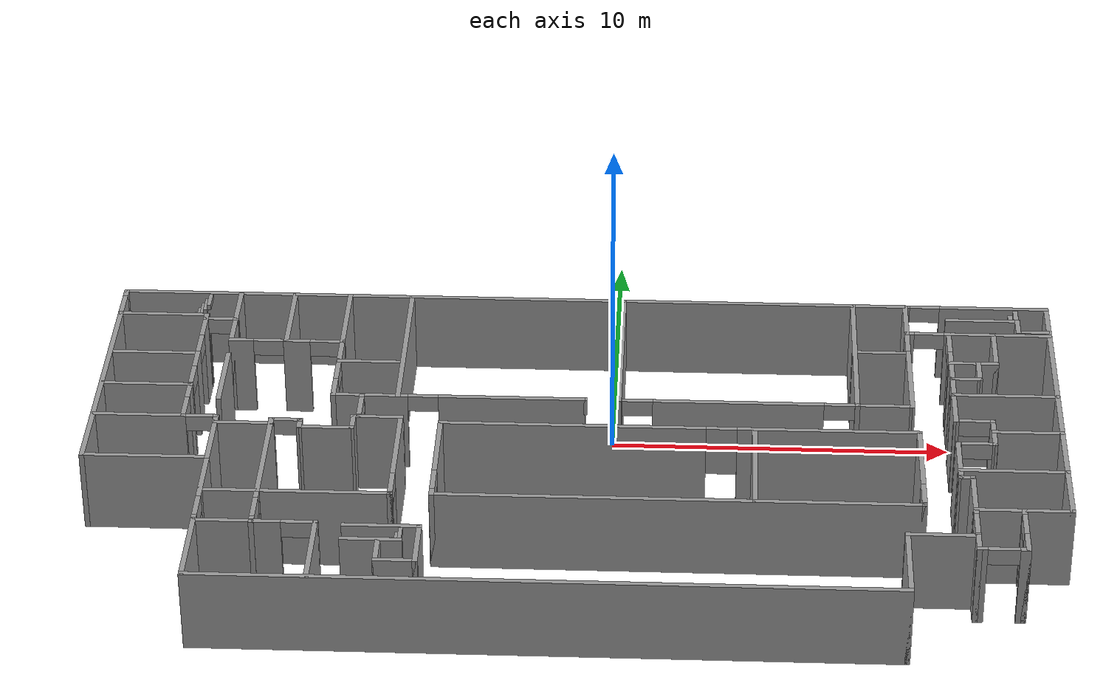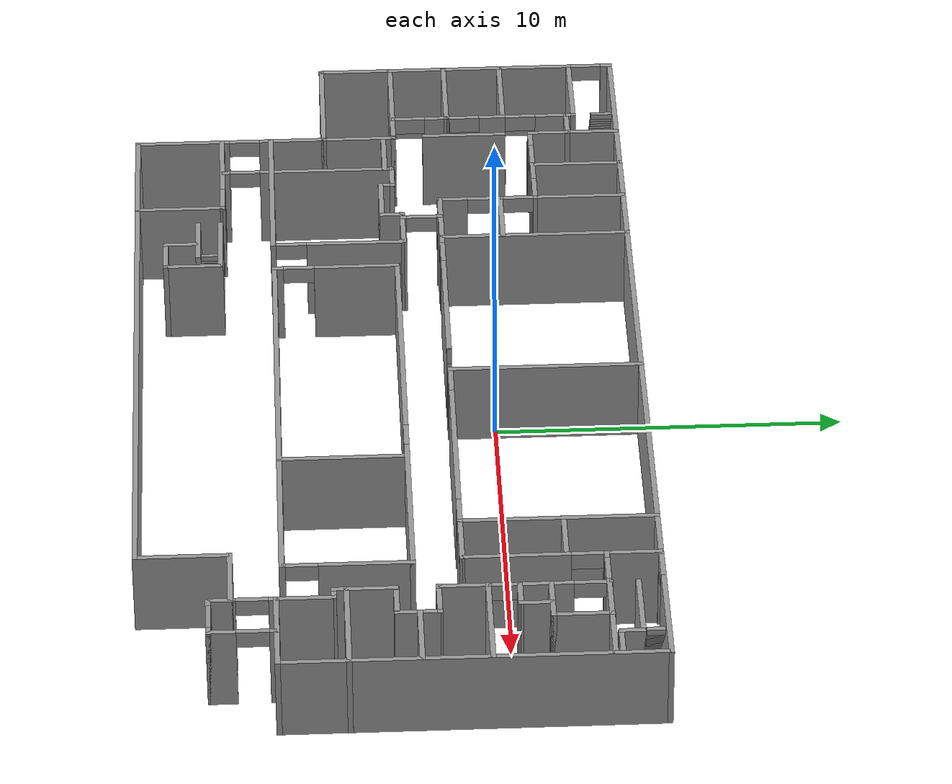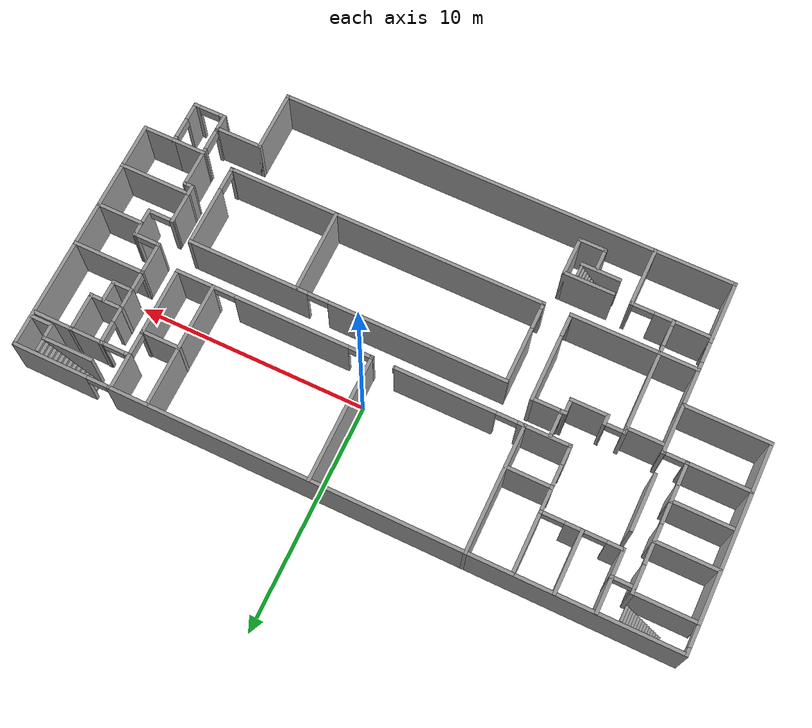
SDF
<?xml version='1.0'?>
<sdf version='1.6'>
  <model name='deh_f1'>
    <pose frame=''>-0.995568 -3.05257 0 0 -0 0</pose>
    <link name='Stairs_0'>
      <visual name='Stairs_0_Visual_0'>
        <pose frame=''>-6.2314 -5.10974 0.083333 0 -0 1.5708</pose>
        <geometry>
          <box>
            <size>0.49 0.113139 0.166667</size>
          </box>
        </geometry>
        <material>
          <script>
            <uri>file://media/materials/scripts/gazebo.material</uri>
            <name>Gazebo/Grey</name>
          </script>
          <ambient>1 1 1 1</ambient>
        </material>
      </visual>
      <collision name='Stairs_0_Collision_0'>
        <geometry>
          <box>
            <size>0.49 0.113139 0.166667</size>
          </box>
        </geometry>
        <pose frame=''>-6.2314 -5.10974 0.083333 0 -0 1.5708</pose>
      </collision>
      <visual name='Stairs_0_Visual_1'>
        <pose frame=''>-6.11826 -5.10974 0.25 0 -0 1.5708</pose>
        <geometry>
          <box>
            <size>0.49 0.113139 0.166667</size>
          </box>
        </geometry>
        <material>
          <script>
            <uri>file://media/materials/scripts/gazebo.material</uri>
            <name>Gazebo/Grey</name>
          </script>
          <ambient>1 1 1 1</ambient>
        </material>
      </visual>
      <collision name='Stairs_0_Collision_1'>
        <geometry>
          <box>
            <size>0.49 0.113139 0.166667</size>
          </box>
        </geometry>
        <pose frame=''>-6.11826 -5.10974 0.25 0 -0 1.5708</pose>
      </collision>
      <visual name='Stairs_0_Visual_2'>
        <pose frame=''>-6.00512 -5.10974 0.416667 0 -0 1.5708</pose>
        <geometry>
          <box>
            <size>0.49 0.113139 0.166667</size>
          </box>
        </geometry>
        <material>
          <script>
            <uri>file://media/materials/scripts/gazebo.material</uri>
            <name>Gazebo/Grey</name>
          </script>
          <ambient>1 1 1 1</ambient>
        </material>
      </visual>
      <collision name='Stairs_0_Collision_2'>
        <geometry>
          <box>
            <size>0.49 0.113139 0.166667</size>
          </box>
        </geometry>
        <pose frame=''>-6.00512 -5.10974 0.416667 0 -0 1.5708</pose>
      </collision>
      <visual name='Stairs_0_Visual_3'>
        <pose frame=''>-5.89198 -5.10974 0.583333 0 -0 1.5708</pose>
        <geometry>
          <box>
            <size>0.49 0.113139 0.166667</size>
          </box>
        </geometry>
        <material>
          <script>
            <uri>file://media/materials/scripts/gazebo.material</uri>
            <name>Gazebo/Grey</name>
          </script>
          <ambient>1 1 1 1</ambient>
        </material>
      </visual>
      <collision name='Stairs_0_Collision_3'>
        <geometry>
          <box>
            <size>0.49 0.113139 0.166667</size>
          </box>
        </geometry>
        <pose frame=''>-5.89198 -5.10974 0.583333 0 -0 1.5708</pose>
      </collision>
      <visual name='Stairs_0_Visual_4'>
        <pose frame=''>-5.77884 -5.10974 0.75 0 -0 1.5708</pose>
        <geometry>
          <box>
            <size>0.49 0.113139 0.166667</size>
          </box>
        </geometry>
        <material>
          <script>
            <uri>file://media/materials/scripts/gazebo.material</uri>
            <name>Gazebo/Grey</name>
          </script>
          <ambient>1 1 1 1</ambient>
        </material>
      </visual>
      <collision name='Stairs_0_Collision_4'>
        <geometry>
          <box>
            <size>0.49 0.113139 0.166667</size>
          </box>
        </geometry>
        <pose frame=''>-5.77884 -5.10974 0.75 0 -0 1.5708</pose>
      </collision>
      <visual name='Stairs_0_Visual_5'>
        <pose frame=''>-5.66571 -5.10974 0.916667 0 -0 1.5708</pose>
        <geometry>
          <box>
            <size>0.49 0.113139 0.166667</size>
          </box>
        </geometry>
        <material>
          <script>
            <uri>file://media/materials/scripts/gazebo.material</uri>
            <name>Gazebo/Grey</name>
          </script>
          <ambient>1 1 1 1</ambient>
        </material>
      </visual>
      <collision name='Stairs_0_Collision_5'>
        <geometry>
          <box>
            <size>0.49 0.113139 0.166667</size>
          </box>
        </geometry>
        <pose frame=''>-5.66571 -5.10974 0.916667 0 -0 1.5708</pose>
      </collision>
      <visual name='Stairs_0_Visual_6'>
        <pose frame=''>-5.55257 -5.10974 1.08333 0 -0 1.5708</pose>
        <geometry>
          <box>
            <size>0.49 0.113139 0.166667</size>
          </box>
        </geometry>
        <material>
          <script>
            <uri>file://media/materials/scripts/gazebo.material</uri>
            <name>Gazebo/Grey</name>
          </script>
          <ambient>1 1 1 1</ambient>
        </material>
      </visual>
      <collision name='Stairs_0_Collision_6'>
        <geometry>
          <box>
            <size>0.49 0.113139 0.166667</size>
          </box>
        </geometry>
        <pose frame=''>-5.55257 -5.10974 1.08333 0 -0 1.5708</pose>
      </collision>
      <visual name='Stairs_0_Visual_7'>
        <pose frame=''>-5.43943 -5.10974 1.25 0 -0 1.5708</pose>
        <geometry>
          <box>
            <size>0.49 0.113139 0.166667</size>
          </box>
        </geometry>
        <material>
          <script>
            <uri>file://media/materials/scripts/gazebo.material</uri>
            <name>Gazebo/Grey</name>
          </script>
          <ambient>1 1 1 1</ambient>
        </material>
      </visual>
      <collision name='Stairs_0_Collision_7'>
        <geometry>
          <box>
            <size>0.49 0.113139 0.166667</size>
          </box>
        </geometry>
        <pose frame=''>-5.43943 -5.10974 1.25 0 -0 1.5708</pose>
      </collision>
      <visual name='Stairs_0_Visual_8'>
        <pose frame=''>-5.32629 -5.10974 1.41667 0 -0 1.5708</pose>
        <geometry>
          <box>
            <size>0.49 0.113139 0.166667</size>
          </box>
        </geometry>
        <material>
          <script>
            <uri>file://media/materials/scripts/gazebo.material</uri>
            <name>Gazebo/Grey</name>
          </script>
          <ambient>1 1 1 1</ambient>
        </material>
      </visual>
      <collision name='Stairs_0_Collision_8'>
        <geometry>
          <box>
            <size>0.49 0.113139 0.166667</size>
          </box>
        </geometry>
        <pose frame=''>-5.32629 -5.10974 1.41667 0 -0 1.5708</pose>
      </collision>
      <visual name='Stairs_0_Visual_9'>
        <pose frame=''>-5.21315 -5.10974 1.58333 0 -0 1.5708</pose>
        <geometry>
          <box>
            <size>0.49 0.113139 0.166667</size>
          </box>
        </geometry>
        <material>
          <script>
            <uri>file://media/materials/scripts/gazebo.material</uri>
            <name>Gazebo/Grey</name>
          </script>
          <ambient>1 1 1 1</ambient>
        </material>
      </visual>
      <collision name='Stairs_0_Collision_9'>
        <geometry>
          <box>
            <size>0.49 0.113139 0.166667</size>
          </box>
        </geometry>
        <pose frame=''>-5.21315 -5.10974 1.58333 0 -0 1.5708</pose>
      </collision>
      <visual name='Stairs_0_Visual_10'>
        <pose frame=''>-5.10001 -5.10974 1.75 0 -0 1.5708</pose>
        <geometry>
          <box>
            <size>0.49 0.113139 0.166667</size>
          </box>
        </geometry>
        <material>
          <script>
            <uri>file://media/materials/scripts/gazebo.material</uri>
            <name>Gazebo/Grey</name>
          </script>
          <ambient>1 1 1 1</ambient>
        </material>
      </visual>
      <collision name='Stairs_0_Collision_10'>
        <geometry>
          <box>
            <size>0.49 0.113139 0.166667</size>
          </box>
        </geometry>
        <pose frame=''>-5.10001 -5.10974 1.75 0 -0 1.5708</pose>
      </collision>
      <visual name='Stairs_0_Visual_11'>
        <pose frame=''>-4.98687 -5.10974 1.91667 0 -0 1.5708</pose>
        <geometry>
          <box>
            <size>0.49 0.113139 0.166667</size>
          </box>
        </geometry>
        <material>
          <script>
            <uri>file://media/materials/scripts/gazebo.material</uri>
            <name>Gazebo/Grey</name>
          </script>
          <ambient>1 1 1 1</ambient>
        </material>
      </visual>
      <collision name='Stairs_0_Collision_11'>
        <geometry>
          <box>
            <size>0.49 0.113139 0.166667</size>
          </box>
        </geometry>
        <pose frame=''>-4.98687 -5.10974 1.91667 0 -0 1.5708</pose>
      </collision>
      <visual name='Stairs_0_Visual_12'>
        <pose frame=''>-4.87373 -5.10974 2.08333 0 -0 1.5708</pose>
        <geometry>
          <box>
            <size>0.49 0.113139 0.166667</size>
          </box>
        </geometry>
        <material>
          <script>
            <uri>file://media/materials/scripts/gazebo.material</uri>
            <name>Gazebo/Grey</name>
          </script>
          <ambient>1 1 1 1</ambient>
        </material>
      </visual>
      <collision name='Stairs_0_Collision_12'>
        <geometry>
          <box>
            <size>0.49 0.113139 0.166667</size>
          </box>
        </geometry>
        <pose frame=''>-4.87373 -5.10974 2.08333 0 -0 1.5708</pose>
      </collision>
      <visual name='Stairs_0_Visual_13'>
        <pose frame=''>-4.76059 -5.10974 2.25 0 -0 1.5708</pose>
        <geometry>
          <box>
            <size>0.49 0.113139 0.166667</size>
          </box>
        </geometry>
        <material>
          <script>
            <uri>file://media/materials/scripts/gazebo.material</uri>
            <name>Gazebo/Grey</name>
          </script>
          <ambient>1 1 1 1</ambient>
        </material>
      </visual>
      <collision name='Stairs_0_Collision_13'>
        <geometry>
          <box>
            <size>0.49 0.113139 0.166667</size>
          </box>
        </geometry>
        <pose frame=''>-4.76059 -5.10974 2.25 0 -0 1.5708</pose>
      </collision>
      <visual name='Stairs_0_Visual_14'>
        <pose frame=''>-4.64745 -5.10974 2.41667 0 -0 1.5708</pose>
        <geometry>
          <box>
            <size>0.49 0.113139 0.166667</size>
          </box>
        </geometry>
        <material>
          <script>
            <uri>file://media/materials/scripts/gazebo.material</uri>
            <name>Gazebo/Grey</name>
          </script>
          <ambient>1 1 1 1</ambient>
        </material>
      </visual>
      <collision name='Stairs_0_Collision_14'>
        <geometry>
          <box>
            <size>0.49 0.113139 0.166667</size>
          </box>
        </geometry>
        <pose frame=''>-4.64745 -5.10974 2.41667 0 -0 1.5708</pose>
      </collision>
    </link>
    <link name='Stairs_1'>
      <visual name='Stairs_1_Visual_0'>
        <pose frame=''>-13.1163 6.81612 0.083333 0 -0 1.5708</pose>
        <geometry>
          <box>
            <size>0.63499 0.119775 0.166667</size>
          </box>
        </geometry>
        <material>
          <script>
            <uri>file://media/materials/scripts/gazebo.material</uri>
            <name>Gazebo/Grey</name>
          </script>
          <ambient>1 1 1 1</ambient>
        </material>
      </visual>
      <collision name='Stairs_1_Collision_0'>
        <geometry>
          <box>
            <size>0.63499 0.119775 0.166667</size>
          </box>
        </geometry>
        <pose frame=''>-13.1163 6.81612 0.083333 0 -0 1.5708</pose>
      </collision>
      <visual name='Stairs_1_Visual_1'>
        <pose frame=''>-12.9965 6.81612 0.25 0 -0 1.5708</pose>
        <geometry>
          <box>
            <size>0.63499 0.119775 0.166667</size>
          </box>
        </geometry>
        <material>
          <script>
            <uri>file://media/materials/scripts/gazebo.material</uri>
            <name>Gazebo/Grey</name>
          </script>
          <ambient>1 1 1 1</ambient>
        </material>
      </visual>
      <collision name='Stairs_1_Collision_1'>
        <geometry>
          <box>
            <size>0.63499 0.119775 0.166667</size>
          </box>
        </geometry>
        <pose frame=''>-12.9965 6.81612 0.25 0 -0 1.5708</pose>
      </collision>
      <visual name='Stairs_1_Visual_2'>
        <pose frame=''>-12.8767 6.81612 0.416667 0 -0 1.5708</pose>
        <geometry>
          <box>
            <size>0.63499 0.119775 0.166667</size>
          </box>
        </geometry>
        <material>
          <script>
            <uri>file://media/materials/scripts/gazebo.material</uri>
            <name>Gazebo/Grey</name>
          </script>
          <ambient>1 1 1 1</ambient>
        </material>
      </visual>
      <collision name='Stairs_1_Collision_2'>
        <geometry>
          <box>
            <size>0.63499 0.119775 0.166667</size>
          </box>
        </geometry>
        <pose frame=''>-12.8767 6.81612 0.416667 0 -0 1.5708</pose>
      </collision>
      <visual name='Stairs_1_Visual_3'>
        <pose frame=''>-12.757 6.81612 0.583333 0 -0 1.5708</pose>
        <geometry>
          <box>
            <size>0.63499 0.119775 0.166667</size>
          </box>
        </geometry>
        <material>
          <script>
            <uri>file://media/materials/scripts/gazebo.material</uri>
            <name>Gazebo/Grey</name>
          </script>
          <ambient>1 1 1 1</ambient>
        </material>
      </visual>
      <collision name='Stairs_1_Collision_3'>
        <geometry>
          <box>
            <size>0.63499 0.119775 0.166667</size>
          </box>
        </geometry>
        <pose frame=''>-12.757 6.81612 0.583333 0 -0 1.5708</pose>
      </collision>
      <visual name='Stairs_1_Visual_4'>
        <pose frame=''>-12.6372 6.81612 0.75 0 -0 1.5708</pose>
        <geometry>
          <box>
            <size>0.63499 0.119775 0.166667</size>
          </box>
        </geometry>
        <material>
          <script>
            <uri>file://media/materials/scripts/gazebo.material</uri>
            <name>Gazebo/Grey</name>
          </script>
          <ambient>1 1 1 1</ambient>
        </material>
      </visual>
      <collision name='Stairs_1_Collision_4'>
        <geometry>
          <box>
            <size>0.63499 0.119775 0.166667</size>
          </box>
        </geometry>
        <pose frame=''>-12.6372 6.81612 0.75 0 -0 1.5708</pose>
      </collision>
      <visual name='Stairs_1_Visual_5'>
        <pose frame=''>-12.5174 6.81612 0.916667 0 -0 1.5708</pose>
        <geometry>
          <box>
            <size>0.63499 0.119775 0.166667</size>
          </box>
        </geometry>
        <material>
          <script>
            <uri>file://media/materials/scripts/gazebo.material</uri>
            <name>Gazebo/Grey</name>
          </script>
          <ambient>1 1 1 1</ambient>
        </material>
      </visual>
      <collision name='Stairs_1_Collision_5'>
        <geometry>
          <box>
            <size>0.63499 0.119775 0.166667</size>
          </box>
        </geometry>
        <pose frame=''>-12.5174 6.81612 0.916667 0 -0 1.5708</pose>
      </collision>
      <visual name='Stairs_1_Visual_6'>
        <pose frame=''>-12.3976 6.81612 1.08333 0 -0 1.5708</pose>
        <geometry>
          <box>
            <size>0.63499 0.119775 0.166667</size>
          </box>
        </geometry>
        <material>
          <script>
            <uri>file://media/materials/scripts/gazebo.material</uri>
            <name>Gazebo/Grey</name>
          </script>
          <ambient>1 1 1 1</ambient>
        </material>
      </visual>
      <collision name='Stairs_1_Collision_6'>
        <geometry>
          <box>
            <size>0.63499 0.119775 0.166667</size>
          </box>
        </geometry>
        <pose frame=''>-12.3976 6.81612 1.08333 0 -0 1.5708</pose>
      </collision>
      <visual name='Stairs_1_Visual_7'>
        <pose frame=''>-12.2779 6.81612 1.25 0 -0 1.5708</pose>
        <geometry>
          <box>
            <size>0.63499 0.119775 0.166667</size>
          </box>
        </geometry>
        <material>
          <script>
            <uri>file://media/materials/scripts/gazebo.material</uri>
            <name>Gazebo/Grey</name>
          </script>
          <ambient>1 1 1 1</ambient>
        </material>
      </visual>
      <collision name='Stairs_1_Collision_7'>
        <geometry>
          <box>
            <size>0.63499 0.119775 0.166667</size>
          </box>
        </geometry>
        <pose frame=''>-12.2779 6.81612 1.25 0 -0 1.5708</pose>
      </collision>
      <visual name='Stairs_1_Visual_8'>
        <pose frame=''>-12.1581 6.81612 1.41667 0 -0 1.5708</pose>
        <geometry>
          <box>
            <size>0.63499 0.119775 0.166667</size>
          </box>
        </geometry>
        <material>
          <script>
            <uri>file://media/materials/scripts/gazebo.material</uri>
            <name>Gazebo/Grey</name>
          </script>
          <ambient>1 1 1 1</ambient>
        </material>
      </visual>
      <collision name='Stairs_1_Collision_8'>
        <geometry>
          <box>
            <size>0.63499 0.119775 0.166667</size>
          </box>
        </geometry>
        <pose frame=''>-12.1581 6.81612 1.41667 0 -0 1.5708</pose>
      </collision>
      <visual name='Stairs_1_Visual_9'>
        <pose frame=''>-12.0383 6.81612 1.58333 0 -0 1.5708</pose>
        <geometry>
          <box>
            <size>0.63499 0.119775 0.166667</size>
          </box>
        </geometry>
        <material>
          <script>
            <uri>file://media/materials/scripts/gazebo.material</uri>
            <name>Gazebo/Grey</name>
          </script>
          <ambient>1 1 1 1</ambient>
        </material>
      </visual>
      <collision name='Stairs_1_Collision_9'>
        <geometry>
          <box>
            <size>0.63499 0.119775 0.166667</size>
          </box>
        </geometry>
        <pose frame=''>-12.0383 6.81612 1.58333 0 -0 1.5708</pose>
      </collision>
      <visual name='Stairs_1_Visual_10'>
        <pose frame=''>-11.9185 6.81612 1.75 0 -0 1.5708</pose>
        <geometry>
          <box>
            <size>0.63499 0.119775 0.166667</size>
          </box>
        </geometry>
        <material>
          <script>
            <uri>file://media/materials/scripts/gazebo.material</uri>
            <name>Gazebo/Grey</name>
          </script>
          <ambient>1 1 1 1</ambient>
        </material>
      </visual>
      <collision name='Stairs_1_Collision_10'>
        <geometry>
          <box>
            <size>0.63499 0.119775 0.166667</size>
          </box>
        </geometry>
        <pose frame=''>-11.9185 6.81612 1.75 0 -0 1.5708</pose>
      </collision>
      <visual name='Stairs_1_Visual_11'>
        <pose frame=''>-11.7988 6.81612 1.91667 0 -0 1.5708</pose>
        <geometry>
          <box>
            <size>0.63499 0.119775 0.166667</size>
          </box>
        </geometry>
        <material>
          <script>
            <uri>file://media/materials/scripts/gazebo.material</uri>
            <name>Gazebo/Grey</name>
          </script>
          <ambient>1 1 1 1</ambient>
        </material>
      </visual>
      <collision name='Stairs_1_Collision_11'>
        <geometry>
          <box>
            <size>0.63499 0.119775 0.166667</size>
          </box>
        </geometry>
        <pose frame=''>-11.7988 6.81612 1.91667 0 -0 1.5708</pose>
      </collision>
      <visual name='Stairs_1_Visual_12'>
        <pose frame=''>-11.679 6.81612 2.08333 0 -0 1.5708</pose>
        <geometry>
          <box>
            <size>0.63499 0.119775 0.166667</size>
          </box>
        </geometry>
        <material>
          <script>
            <uri>file://media/materials/scripts/gazebo.material</uri>
            <name>Gazebo/Grey</name>
          </script>
          <ambient>1 1 1 1</ambient>
        </material>
      </visual>
      <collision name='Stairs_1_Collision_12'>
        <geometry>
          <box>
            <size>0.63499 0.119775 0.166667</size>
          </box>
        </geometry>
        <pose frame=''>-11.679 6.81612 2.08333 0 -0 1.5708</pose>
      </collision>
      <visual name='Stairs_1_Visual_13'>
        <pose frame=''>-11.5592 6.81612 2.25 0 -0 1.5708</pose>
        <geometry>
          <box>
            <size>0.63499 0.119775 0.166667</size>
          </box>
        </geometry>
        <material>
          <script>
            <uri>file://media/materials/scripts/gazebo.material</uri>
            <name>Gazebo/Grey</name>
          </script>
          <ambient>1 1 1 1</ambient>
        </material>
      </visual>
      <collision name='Stairs_1_Collision_13'>
        <geometry>
          <box>
            <size>0.63499 0.119775 0.166667</size>
          </box>
        </geometry>
        <pose frame=''>-11.5592 6.81612 2.25 0 -0 1.5708</pose>
      </collision>
      <visual name='Stairs_1_Visual_14'>
        <pose frame=''>-11.4394 6.81612 2.41667 0 -0 1.5708</pose>
        <geometry>
          <box>
            <size>0.63499 0.119775 0.166667</size>
          </box>
        </geometry>
        <material>
          <script>
            <uri>file://media/materials/scripts/gazebo.material</uri>
            <name>Gazebo/Grey</name>
          </script>
          <ambient>1 1 1 1</ambient>
        </material>
      </visual>
      <collision name='Stairs_1_Collision_14'>
        <geometry>
          <box>
            <size>0.63499 0.119775 0.166667</size>
          </box>
        </geometry>
        <pose frame=''>-11.4394 6.81612 2.41667 0 -0 1.5708</pose>
      </collision>
    </link>
    <link name='Stairs_2'>
      <visual name='Stairs_2_Visual_0'>
        <pose frame=''>11.0741 6.86907 0.083333 0 -0 1.5708</pose>
        <geometry>
          <box>
            <size>0.520025 0.144952 0.166667</size>
          </box>
        </geometry>
        <material>
          <script>
            <uri>file://media/materials/scripts/gazebo.material</uri>
            <name>Gazebo/Grey</name>
          </script>
          <ambient>1 1 1 1</ambient>
        </material>
      </visual>
      <collision name='Stairs_2_Collision_0'>
        <geometry>
          <box>
            <size>0.520025 0.144952 0.166667</size>
          </box>
        </geometry>
        <pose frame=''>11.0741 6.86907 0.083333 0 -0 1.5708</pose>
      </collision>
      <visual name='Stairs_2_Visual_1'>
        <pose frame=''>11.219 6.86907 0.25 0 -0 1.5708</pose>
        <geometry>
          <box>
            <size>0.520025 0.144952 0.166667</size>
          </box>
        </geometry>
        <material>
          <script>
            <uri>file://media/materials/scripts/gazebo.material</uri>
            <name>Gazebo/Grey</name>
          </script>
          <ambient>1 1 1 1</ambient>
        </material>
      </visual>
      <collision name='Stairs_2_Collision_1'>
        <geometry>
          <box>
            <size>0.520025 0.144952 0.166667</size>
          </box>
        </geometry>
        <pose frame=''>11.219 6.86907 0.25 0 -0 1.5708</pose>
      </collision>
      <visual name='Stairs_2_Visual_2'>
        <pose frame=''>11.364 6.86907 0.416667 0 -0 1.5708</pose>
        <geometry>
          <box>
            <size>0.520025 0.144952 0.166667</size>
          </box>
        </geometry>
        <material>
          <script>
            <uri>file://media/materials/scripts/gazebo.material</uri>
            <name>Gazebo/Grey</name>
          </script>
          <ambient>1 1 1 1</ambient>
        </material>
      </visual>
      <collision name='Stairs_2_Collision_2'>
        <geometry>
          <box>
            <size>0.520025 0.144952 0.166667</size>
          </box>
        </geometry>
        <pose frame=''>11.364 6.86907 0.416667 0 -0 1.5708</pose>
      </collision>
      <visual name='Stairs_2_Visual_3'>
        <pose frame=''>11.5089 6.86907 0.583333 0 -0 1.5708</pose>
        <geometry>
          <box>
            <size>0.520025 0.144952 0.166667</size>
          </box>
        </geometry>
        <material>
          <script>
            <uri>file://media/materials/scripts/gazebo.material</uri>
            <name>Gazebo/Grey</name>
          </script>
          <ambient>1 1 1 1</ambient>
        </material>
      </visual>
      <collision name='Stairs_2_Collision_3'>
        <geometry>
          <box>
            <size>0.520025 0.144952 0.166667</size>
          </box>
        </geometry>
        <pose frame=''>11.5089 6.86907 0.583333 0 -0 1.5708</pose>
      </collision>
      <visual name='Stairs_2_Visual_4'>
        <pose frame=''>11.6539 6.86907 0.75 0 -0 1.5708</pose>
        <geometry>
          <box>
            <size>0.520025 0.144952 0.166667</size>
          </box>
        </geometry>
        <material>
          <script>
            <uri>file://media/materials/scripts/gazebo.material</uri>
            <name>Gazebo/Grey</name>
          </script>
          <ambient>1 1 1 1</ambient>
        </material>
      </visual>
      <collision name='Stairs_2_Collision_4'>
        <geometry>
          <box>
            <size>0.520025 0.144952 0.166667</size>
          </box>
        </geometry>
        <pose frame=''>11.6539 6.86907 0.75 0 -0 1.5708</pose>
      </collision>
      <visual name='Stairs_2_Visual_5'>
        <pose frame=''>11.7988 6.86907 0.916667 0 -0 1.5708</pose>
        <geometry>
          <box>
            <size>0.520025 0.144952 0.166667</size>
          </box>
        </geometry>
        <material>
          <script>
            <uri>file://media/materials/scripts/gazebo.material</uri>
            <name>Gazebo/Grey</name>
          </script>
          <ambient>1 1 1 1</ambient>
        </material>
      </visual>
      <collision name='Stairs_2_Collision_5'>
        <geometry>
          <box>
            <size>0.520025 0.144952 0.166667</size>
          </box>
        </geometry>
        <pose frame=''>11.7988 6.86907 0.916667 0 -0 1.5708</pose>
      </collision>
      <visual name='Stairs_2_Visual_6'>
        <pose frame=''>11.9438 6.86907 1.08333 0 -0 1.5708</pose>
        <geometry>
          <box>
            <size>0.520025 0.144952 0.166667</size>
          </box>
        </geometry>
        <material>
          <script>
            <uri>file://media/materials/scripts/gazebo.material</uri>
            <name>Gazebo/Grey</name>
          </script>
          <ambient>1 1 1 1</ambient>
        </material>
      </visual>
      <collision name='Stairs_2_Collision_6'>
        <geometry>
          <box>
            <size>0.520025 0.144952 0.166667</size>
          </box>
        </geometry>
        <pose frame=''>11.9438 6.86907 1.08333 0 -0 1.5708</pose>
      </collision>
      <visual name='Stairs_2_Visual_7'>
        <pose frame=''>12.0887 6.86907 1.25 0 -0 1.5708</pose>
        <geometry>
          <box>
            <size>0.520025 0.144952 0.166667</size>
          </box>
        </geometry>
        <material>
          <script>
            <uri>file://media/materials/scripts/gazebo.material</uri>
            <name>Gazebo/Grey</name>
          </script>
          <ambient>1 1 1 1</ambient>
        </material>
      </visual>
      <collision name='Stairs_2_Collision_7'>
        <geometry>
          <box>
            <size>0.520025 0.144952 0.166667</size>
          </box>
        </geometry>
        <pose frame=''>12.0887 6.86907 1.25 0 -0 1.5708</pose>
      </collision>
      <visual name='Stairs_2_Visual_8'>
        <pose frame=''>12.2337 6.86907 1.41667 0 -0 1.5708</pose>
        <geometry>
          <box>
            <size>0.520025 0.144952 0.166667</size>
          </box>
        </geometry>
        <material>
          <script>
            <uri>file://media/materials/scripts/gazebo.material</uri>
            <name>Gazebo/Grey</name>
          </script>
          <ambient>1 1 1 1</ambient>
        </material>
      </visual>
      <collision name='Stairs_2_Collision_8'>
        <geometry>
          <box>
            <size>0.520025 0.144952 0.166667</size>
          </box>
        </geometry>
        <pose frame=''>12.2337 6.86907 1.41667 0 -0 1.5708</pose>
      </collision>
      <visual name='Stairs_2_Visual_9'>
        <pose frame=''>12.3786 6.86907 1.58333 0 -0 1.5708</pose>
        <geometry>
          <box>
            <size>0.520025 0.144952 0.166667</size>
          </box>
        </geometry>
        <material>
          <script>
            <uri>file://media/materials/scripts/gazebo.material</uri>
            <name>Gazebo/Grey</name>
          </script>
          <ambient>1 1 1 1</ambient>
        </material>
      </visual>
      <collision name='Stairs_2_Collision_9'>
        <geometry>
          <box>
            <size>0.520025 0.144952 0.166667</size>
          </box>
        </geometry>
        <pose frame=''>12.3786 6.86907 1.58333 0 -0 1.5708</pose>
      </collision>
      <visual name='Stairs_2_Visual_10'>
        <pose frame=''>12.5236 6.86907 1.75 0 -0 1.5708</pose>
        <geometry>
          <box>
            <size>0.520025 0.144952 0.166667</size>
          </box>
        </geometry>
        <material>
          <script>
            <uri>file://media/materials/scripts/gazebo.material</uri>
            <name>Gazebo/Grey</name>
          </script>
          <ambient>1 1 1 1</ambient>
        </material>
      </visual>
      <collision name='Stairs_2_Collision_10'>
        <geometry>
          <box>
            <size>0.520025 0.144952 0.166667</size>
          </box>
        </geometry>
        <pose frame=''>12.5236 6.86907 1.75 0 -0 1.5708</pose>
      </collision>
      <visual name='Stairs_2_Visual_11'>
        <pose frame=''>12.6685 6.86907 1.91667 0 -0 1.5708</pose>
        <geometry>
          <box>
            <size>0.520025 0.144952 0.166667</size>
          </box>
        </geometry>
        <material>
          <script>
            <uri>file://media/materials/scripts/gazebo.material</uri>
            <name>Gazebo/Grey</name>
          </script>
          <ambient>1 1 1 1</ambient>
        </material>
      </visual>
      <collision name='Stairs_2_Collision_11'>
        <geometry>
          <box>
            <size>0.520025 0.144952 0.166667</size>
          </box>
        </geometry>
        <pose frame=''>12.6685 6.86907 1.91667 0 -0 1.5708</pose>
      </collision>
      <visual name='Stairs_2_Visual_12'>
        <pose frame=''>12.8135 6.86907 2.08333 0 -0 1.5708</pose>
        <geometry>
          <box>
            <size>0.520025 0.144952 0.166667</size>
          </box>
        </geometry>
        <material>
          <script>
            <uri>file://media/materials/scripts/gazebo.material</uri>
            <name>Gazebo/Grey</name>
          </script>
          <ambient>1 1 1 1</ambient>
        </material>
      </visual>
      <collision name='Stairs_2_Collision_12'>
        <geometry>
          <box>
            <size>0.520025 0.144952 0.166667</size>
          </box>
        </geometry>
        <pose frame=''>12.8135 6.86907 2.08333 0 -0 1.5708</pose>
      </collision>
      <visual name='Stairs_2_Visual_13'>
        <pose frame=''>12.9584 6.86907 2.25 0 -0 1.5708</pose>
        <geometry>
          <box>
            <size>0.520025 0.144952 0.166667</size>
          </box>
        </geometry>
        <material>
          <script>
            <uri>file://media/materials/scripts/gazebo.material</uri>
            <name>Gazebo/Grey</name>
          </script>
          <ambient>1 1 1 1</ambient>
        </material>
      </visual>
      <collision name='Stairs_2_Collision_13'>
        <geometry>
          <box>
            <size>0.520025 0.144952 0.166667</size>
          </box>
        </geometry>
        <pose frame=''>12.9584 6.86907 2.25 0 -0 1.5708</pose>
      </collision>
      <visual name='Stairs_2_Visual_14'>
        <pose frame=''>13.1034 6.86907 2.41667 0 -0 1.5708</pose>
        <geometry>
          <box>
            <size>0.520025 0.144952 0.166667</size>
          </box>
        </geometry>
        <material>
          <script>
            <uri>file://media/materials/scripts/gazebo.material</uri>
            <name>Gazebo/Grey</name>
          </script>
          <ambient>1 1 1 1</ambient>
        </material>
      </visual>
      <collision name='Stairs_2_Collision_14'>
        <geometry>
          <box>
            <size>0.520025 0.144952 0.166667</size>
          </box>
        </geometry>
        <pose frame=''>13.1034 6.86907 2.41667 0 -0 1.5708</pose>
      </collision>
    </link>
    <link name='Wall_0'>
      <collision name='Wall_0_Collision'>
        <geometry>
          <box>
            <size>20 0.15 2.5</size>
          </box>
        </geometry>
        <pose frame=''>0 0 1.25 0 -0 0</pose>
      </collision>
      <visual name='Wall_0_Visual'>
        <pose frame=''>0 0 1.25 0 -0 0</pose>
        <geometry>
          <box>
            <size>20 0.15 2.5</size>
          </box>
        </geometry>
        <material>
          <script>
            <uri>file://media/materials/scripts/gazebo.material</uri>
            <name>Gazebo/Grey</name>
          </script>
          <ambient>1 1 1 1</ambient>
        </material>
      </visual>
      <pose frame=''>-0.526964 -7.22647 0 0 -0 0</pose>
    </link>
    <link name='Wall_10'>
      <collision name='Wall_10_Collision'>
        <geometry>
          <box>
            <size>0.75 0.15 2.5</size>
          </box>
        </geometry>
        <pose frame=''>0 0 1.25 0 -0 0</pose>
      </collision>
      <visual name='Wall_10_Visual'>
        <pose frame=''>0 0 1.25 0 -0 0</pose>
        <geometry>
          <box>
            <size>0.75 0.15 2.5</size>
          </box>
        </geometry>
        <material>
          <script>
            <uri>file://media/materials/scripts/gazebo.material</uri>
            <name>Gazebo/Grey</name>
          </script>
          <ambient>1 1 1 1</ambient>
        </material>
      </visual>
      <pose frame=''>11.348 -4.92647 0 0 -0 1.5708</pose>
    </link>
    <link name='Wall_101'>
      <collision name='Wall_101_Collision'>
        <geometry>
          <box>
            <size>5.6204 0.15 2.5</size>
          </box>
        </geometry>
        <pose frame=''>0 0 1.25 0 -0 0</pose>
      </collision>
      <visual name='Wall_101_Visual'>
        <pose frame=''>0 0 1.25 0 -0 0</pose>
        <geometry>
          <box>
            <size>5.6204 0.15 2.5</size>
          </box>
        </geometry>
        <material>
          <script>
            <uri>file://media/materials/scripts/gazebo.material</uri>
            <name>Gazebo/Grey</name>
          </script>
          <ambient>1 1 1 1</ambient>
        </material>
      </visual>
      <pose frame=''>-5.26917 4.49123 0 0 -0 1.57128</pose>
    </link>
    <link name='Wall_103'>
      <collision name='Wall_103_Collision'>
        <geometry>
          <box>
            <size>2 0.15 2.5</size>
          </box>
        </geometry>
        <pose frame=''>0 0 1.25 0 -0 0</pose>
      </collision>
      <visual name='Wall_103_Visual'>
        <pose frame=''>0 0 1.25 0 -0 0</pose>
        <geometry>
          <box>
            <size>2 0.15 2.5</size>
          </box>
        </geometry>
        <material>
          <script>
            <uri>file://media/materials/scripts/gazebo.material</uri>
            <name>Gazebo/Grey</name>
          </script>
          <ambient>1 1 1 1</ambient>
        </material>
      </visual>
      <pose frame=''>-6.238 3.5569 0 0 -0 0</pose>
    </link>
    <link name='Wall_105'>
      <pose frame=''>-10.9717 5.7489 0 0 -0 3.14159</pose>
      <visual name='Wall_105_Visual_0'>
        <pose frame=''>-0.453629 0 1.25 0 -0 0</pose>
        <geometry>
          <box>
            <size>0.165238 0.15 2.5</size>
          </box>
        </geometry>
        <material>
          <script>
            <uri>file://media/materials/scripts/gazebo.material</uri>
            <name>Gazebo/Grey</name>
          </script>
          <ambient>1 1 1 1</ambient>
        </material>
      </visual>
      <collision name='Wall_105_Collision_0'>
        <geometry>
          <box>
            <size>0.165238 0.15 2.5</size>
          </box>
        </geometry>
        <pose frame=''>-0.453629 0 1.25 0 -0 0</pose>
      </collision>
      <visual name='Wall_105_Visual_1'>
        <pose frame=''>0.457005 0 1.25 0 -0 0</pose>
        <geometry>
          <box>
            <size>0.158486 0.15 2.5</size>
          </box>
        </geometry>
        <material>
          <script>
            <uri>file://media/materials/scripts/gazebo.material</uri>
            <name>Gazebo/Grey</name>
          </script>
          <ambient>1 1 1 1</ambient>
        </material>
      </visual>
      <collision name='Wall_105_Collision_1'>
        <geometry>
          <box>
            <size>0.158486 0.15 2.5</size>
          </box>
        </geometry>
        <pose frame=''>0.457005 0 1.25 0 -0 0</pose>
      </collision>
      <visual name='Wall_105_Visual_2'>
        <pose frame=''>0.003376 0 2.25 0 -0 0</pose>
        <geometry>
          <box>
            <size>0.748771 0.15 0.5</size>
          </box>
        </geometry>
        <material>
          <script>
            <uri>file://media/materials/scripts/gazebo.material</uri>
            <name>Gazebo/Grey</name>
          </script>
          <ambient>1 1 1 1</ambient>
        </material>
      </visual>
      <collision name='Wall_105_Collision_2'>
        <geometry>
          <box>
            <size>0.748771 0.15 0.5</size>
          </box>
        </geometry>
        <pose frame=''>0.003376 0 2.25 0 -0 0</pose>
      </collision>
    </link>
    <link name='Wall_107'>
      <collision name='Wall_107_Collision'>
        <geometry>
          <box>
            <size>5.62515 0.15 2.5</size>
          </box>
        </geometry>
        <pose frame=''>0 0 1.25 0 -0 0</pose>
      </collision>
      <visual name='Wall_107_Visual'>
        <pose frame=''>0 0 1.25 0 -0 0</pose>
        <geometry>
          <box>
            <size>5.62515 0.15 2.5</size>
          </box>
        </geometry>
        <material>
          <script>
            <uri>file://media/materials/scripts/gazebo.material</uri>
            <name>Gazebo/Grey</name>
          </script>
          <ambient>1 1 1 1</ambient>
        </material>
      </visual>
      <pose frame=''>1.21165 4.48247 0 0 0 -1.5708</pose>
    </link>
    <link name='Wall_109'>
      <collision name='Wall_109_Collision'>
        <geometry>
          <box>
            <size>1.75 0.15 2.5</size>
          </box>
        </geometry>
        <pose frame=''>0 0 1.25 0 -0 0</pose>
      </collision>
      <visual name='Wall_109_Visual'>
        <pose frame=''>0 0 1.25 0 -0 0</pose>
        <geometry>
          <box>
            <size>1.75 0.15 2.5</size>
          </box>
        </geometry>
        <material>
          <script>
            <uri>file://media/materials/scripts/gazebo.material</uri>
            <name>Gazebo/Grey</name>
          </script>
          <ambient>1 1 1 1</ambient>
        </material>
      </visual>
      <pose frame=''>8.97986 1.75239 0 0 -0 0</pose>
    </link>
    <link name='Wall_110'>
      <pose frame=''>9.77348 4.47484 0 0 -0 1.57314</pose>
      <visual name='Wall_110_Visual_0'>
        <pose frame=''>-1.26286 0 1.25 0 -0 0</pose>
        <geometry>
          <box>
            <size>3.06917 0.15 2.5</size>
          </box>
        </geometry>
        <material>
          <script>
            <uri>file://media/materials/scripts/gazebo.material</uri>
            <name>Gazebo/Grey</name>
          </script>
          <ambient>1 1 1 1</ambient>
        </material>
      </visual>
      <collision name='Wall_110_Collision_0'>
        <geometry>
          <box>
            <size>3.06917 0.15 2.5</size>
          </box>
        </geometry>
        <pose frame=''>-1.26286 0 1.25 0 -0 0</pose>
      </collision>
      <visual name='Wall_110_Visual_1'>
        <pose frame=''>1.98459 0 1.25 0 -0 0</pose>
        <geometry>
          <box>
            <size>1.62573 0.15 2.5</size>
          </box>
        </geometry>
        <material>
          <script>
            <uri>file://media/materials/scripts/gazebo.material</uri>
            <name>Gazebo/Grey</name>
          </script>
          <ambient>1 1 1 1</ambient>
        </material>
      </visual>
      <collision name='Wall_110_Collision_1'>
        <geometry>
          <box>
            <size>1.62573 0.15 2.5</size>
          </box>
        </geometry>
        <pose frame=''>1.98459 0 1.25 0 -0 0</pose>
      </collision>
      <visual name='Wall_110_Visual_2'>
        <pose frame=''>0.721725 0 2.25 0 -0 0</pose>
        <geometry>
          <box>
            <size>0.9 0.15 0.5</size>
          </box>
        </geometry>
        <material>
          <script>
            <uri>file://media/materials/scripts/gazebo.material</uri>
            <name>Gazebo/Grey</name>
          </script>
          <ambient>1 1 1 1</ambient>
        </material>
      </visual>
      <collision name='Wall_110_Collision_2'>
        <geometry>
          <box>
            <size>0.9 0.15 0.5</size>
          </box>
        </geometry>
        <pose frame=''>0.721725 0 2.25 0 -0 0</pose>
      </collision>
    </link>
    <link name='Wall_114'>
      <pose frame=''>11.9124 5.72672 0 0 -0 0</pose>
      <visual name='Wall_114_Visual_0'>
        <pose frame=''>-2.0611 0 1.25 0 -0 0</pose>
        <geometry>
          <box>
            <size>0.273024 0.15 2.5</size>
          </box>
        </geometry>
        <material>
          <script>
            <uri>file://media/materials/scripts/gazebo.material</uri>
            <name>Gazebo/Grey</name>
          </script>
          <ambient>1 1 1 1</ambient>
        </material>
      </visual>
      <collision name='Wall_114_Collision_0'>
        <geometry>
          <box>
            <size>0.273024 0.15 2.5</size>
          </box>
        </geometry>
        <pose frame=''>-2.0611 0 1.25 0 -0 0</pose>
      </collision>
      <visual name='Wall_114_Visual_1'>
        <pose frame=''>0.586512 0 1.25 0 -0 0</pose>
        <geometry>
          <box>
            <size>3.2222 0.15 2.5</size>
          </box>
        </geometry>
        <material>
          <script>
            <uri>file://media/materials/scripts/gazebo.material</uri>
            <name>Gazebo/Grey</name>
          </script>
          <ambient>1 1 1 1</ambient>
        </material>
      </visual>
      <collision name='Wall_114_Collision_1'>
        <geometry>
          <box>
            <size>3.2222 0.15 2.5</size>
          </box>
        </geometry>
        <pose frame=''>0.586512 0 1.25 0 -0 0</pose>
      </collision>
      <visual name='Wall_114_Visual_2'>
        <pose frame=''>-1.47459 0 2.25 0 -0 0</pose>
        <geometry>
          <box>
            <size>0.9 0.15 0.5</size>
          </box>
        </geometry>
        <material>
          <script>
            <uri>file://media/materials/scripts/gazebo.material</uri>
            <name>Gazebo/Grey</name>
          </script>
          <ambient>1 1 1 1</ambient>
        </material>
      </visual>
      <collision name='Wall_114_Collision_2'>
        <geometry>
          <box>
            <size>0.9 0.15 0.5</size>
          </box>
        </geometry>
        <pose frame=''>-1.47459 0 2.25 0 -0 0</pose>
      </collision>
    </link>
    <link name='Wall_116'>
      <pose frame=''>11.0229 4.08144 0 0 0 -1.5708</pose>
      <visual name='Wall_116_Visual_0'>
        <pose frame=''>-1.65988 0 1.25 0 -0 0</pose>
        <geometry>
          <box>
            <size>0.160376 0.15 2.5</size>
          </box>
        </geometry>
        <material>
          <script>
            <uri>file://media/materials/scripts/gazebo.material</uri>
            <name>Gazebo/Grey</name>
          </script>
          <ambient>1 1 1 1</ambient>
        </material>
      </visual>
      <collision name='Wall_116_Collision_0'>
        <geometry>
          <box>
            <size>0.160376 0.15 2.5</size>
          </box>
        </geometry>
        <pose frame=''>-1.65988 0 1.25 0 -0 0</pose>
      </collision>
      <visual name='Wall_116_Visual_1'>
        <pose frame=''>0.093656 0 1.25 0 -0 0</pose>
        <geometry>
          <box>
            <size>1.54669 0.15 2.5</size>
          </box>
        </geometry>
        <material>
          <script>
            <uri>file://media/materials/scripts/gazebo.material</uri>
            <name>Gazebo/Grey</name>
          </script>
          <ambient>1 1 1 1</ambient>
        </material>
      </visual>
      <collision name='Wall_116_Collision_1'>
        <geometry>
          <box>
            <size>1.54669 0.15 2.5</size>
          </box>
        </geometry>
        <pose frame=''>0.093656 0 1.25 0 -0 0</pose>
      </collision>
      <visual name='Wall_116_Visual_2'>
        <pose frame=''>1.66388 0 1.25 0 -0 0</pose>
        <geometry>
          <box>
            <size>0.152369 0.15 2.5</size>
          </box>
        </geometry>
        <material>
          <script>
            <uri>file://media/materials/scripts/gazebo.material</uri>
            <name>Gazebo/Grey</name>
          </script>
          <ambient>1 1 1 1</ambient>
        </material>
      </visual>
      <collision name='Wall_116_Collision_2'>
        <geometry>
          <box>
            <size>0.152369 0.15 2.5</size>
          </box>
        </geometry>
        <pose frame=''>1.66388 0 1.25 0 -0 0</pose>
      </collision>
      <visual name='Wall_116_Visual_3'>
        <pose frame=''>-1.12969 0 2.25 0 -0 0</pose>
        <geometry>
          <box>
            <size>0.9 0.15 0.5</size>
          </box>
        </geometry>
        <material>
          <script>
            <uri>file://media/materials/scripts/gazebo.material</uri>
            <name>Gazebo/Grey</name>
          </script>
          <ambient>1 1 1 1</ambient>
        </material>
      </visual>
      <collision name='Wall_116_Collision_3'>
        <geometry>
          <box>
            <size>0.9 0.15 0.5</size>
          </box>
        </geometry>
        <pose frame=''>-1.12969 0 2.25 0 -0 0</pose>
      </collision>
      <visual name='Wall_116_Visual_4'>
        <pose frame=''>1.22735 0 2.25 0 -0 0</pose>
        <geometry>
          <box>
            <size>0.720696 0.15 0.5</size>
          </box>
        </geometry>
        <material>
          <script>
            <uri>file://media/materials/scripts/gazebo.material</uri>
            <name>Gazebo/Grey</name>
          </script>
          <ambient>1 1 1 1</ambient>
        </material>
      </visual>
      <collision name='Wall_116_Collision_4'>
        <geometry>
          <box>
            <size>0.720696 0.15 0.5</size>
          </box>
        </geometry>
        <pose frame=''>1.22735 0 2.25 0 -0 0</pose>
      </collision>
    </link>
    <link name='Wall_117'>
      <collision name='Wall_117_Collision'>
        <geometry>
          <box>
            <size>3.16787 0.15 2.5</size>
          </box>
        </geometry>
        <pose frame=''>0 0 1.25 0 -0 0</pose>
      </collision>
      <visual name='Wall_117_Visual'>
        <pose frame=''>0 0 1.25 0 -0 0</pose>
        <geometry>
          <box>
            <size>3.16787 0.15 2.5</size>
          </box>
        </geometry>
        <material>
          <script>
            <uri>file://media/materials/scripts/gazebo.material</uri>
            <name>Gazebo/Grey</name>
          </script>
          <ambient>1 1 1 1</ambient>
        </material>
      </visual>
      <pose frame=''>12.5218 2.4204 0 0 -0 0.002627</pose>
    </link>
    <link name='Wall_119'>
      <collision name='Wall_119_Collision'>
        <geometry>
          <box>
            <size>1.5 0.15 2.5</size>
          </box>
        </geometry>
        <pose frame=''>0 0 1.25 0 -0 0</pose>
      </collision>
      <visual name='Wall_119_Visual'>
        <pose frame=''>0 0 1.25 0 -0 0</pose>
        <geometry>
          <box>
            <size>1.5 0.15 2.5</size>
          </box>
        </geometry>
        <material>
          <script>
            <uri>file://media/materials/scripts/gazebo.material</uri>
            <name>Gazebo/Grey</name>
          </script>
          <ambient>1 1 1 1</ambient>
        </material>
      </visual>
      <pose frame=''>11.6872 4.13684 0 0 -0 0</pose>
    </link>
    <link name='Wall_12'>
      <collision name='Wall_12_Collision'>
        <geometry>
          <box>
            <size>2.75 0.15 2.5</size>
          </box>
        </geometry>
        <pose frame=''>0 0 1.25 0 -0 0</pose>
      </collision>
      <visual name='Wall_12_Visual'>
        <pose frame=''>0 0 1.25 0 -0 0</pose>
        <geometry>
          <box>
            <size>2.75 0.15 2.5</size>
          </box>
        </geometry>
        <material>
          <script>
            <uri>file://media/materials/scripts/gazebo.material</uri>
            <name>Gazebo/Grey</name>
          </script>
          <ambient>1 1 1 1</ambient>
        </material>
      </visual>
      <pose frame=''>9.39804 -5.92647 0 0 -0 1.5708</pose>
    </link>
    <link name='Wall_120'>
      <collision name='Wall_120_Collision'>
        <geometry>
          <box>
            <size>1.75 0.15 2.5</size>
          </box>
        </geometry>
        <pose frame=''>0 0 1.25 0 -0 0</pose>
      </collision>
      <visual name='Wall_120_Visual'>
        <pose frame=''>0 0 1.25 0 -0 0</pose>
        <geometry>
          <box>
            <size>1.75 0.15 2.5</size>
          </box>
        </geometry>
        <material>
          <script>
            <uri>file://media/materials/scripts/gazebo.material</uri>
            <name>Gazebo/Grey</name>
          </script>
          <ambient>1 1 1 1</ambient>
        </material>
      </visual>
      <pose frame=''>12.3622 4.93684 0 0 -0 1.5708</pose>
    </link>
    <link name='Wall_122'>
      <collision name='Wall_122_Collision'>
        <geometry>
          <box>
            <size>1 0.15 2.5</size>
          </box>
        </geometry>
        <pose frame=''>0 0 1.25 0 -0 0</pose>
      </collision>
      <visual name='Wall_122_Visual'>
        <pose frame=''>0 0 1.25 0 -0 0</pose>
        <geometry>
          <box>
            <size>1 0.15 2.5</size>
          </box>
        </geometry>
        <material>
          <script>
            <uri>file://media/materials/scripts/gazebo.material</uri>
            <name>Gazebo/Grey</name>
          </script>
          <ambient>1 1 1 1</ambient>
        </material>
      </visual>
      <pose frame=''>11.8301 3.70041 0 0 0 -1.5708</pose>
    </link>
    <link name='Wall_123'>
      <collision name='Wall_123_Collision'>
        <geometry>
          <box>
            <size>0.951518 0.15 2.5</size>
          </box>
        </geometry>
        <pose frame=''>0 0 1.25 0 -0 0</pose>
      </collision>
      <visual name='Wall_123_Visual'>
        <pose frame=''>0 0 1.25 0 -0 0</pose>
        <geometry>
          <box>
            <size>0.951518 0.15 2.5</size>
          </box>
        </geometry>
        <material>
          <script>
            <uri>file://media/materials/scripts/gazebo.material</uri>
            <name>Gazebo/Grey</name>
          </script>
          <ambient>1 1 1 1</ambient>
        </material>
      </visual>
      <pose frame=''>11.4294 3.27697 0 0 -0 3.1377</pose>
    </link>
    <link name='Wall_125'>
      <collision name='Wall_125_Collision'>
        <geometry>
          <box>
            <size>1.75 0.15 2.5</size>
          </box>
        </geometry>
        <pose frame=''>0 0 1.25 0 -0 0</pose>
      </collision>
      <visual name='Wall_125_Visual'>
        <pose frame=''>0 0 1.25 0 -0 0</pose>
        <geometry>
          <box>
            <size>1.75 0.15 2.5</size>
          </box>
        </geometry>
        <material>
          <script>
            <uri>file://media/materials/scripts/gazebo.material</uri>
            <name>Gazebo/Grey</name>
          </script>
          <ambient>1 1 1 1</ambient>
        </material>
      </visual>
      <pose frame=''>8.97011 4.62775 0 0 -0 3.14159</pose>
    </link>
    <link name='Wall_127'>
      <collision name='Wall_127_Collision'>
        <geometry>
          <box>
            <size>14 0.15 2.5</size>
          </box>
        </geometry>
        <pose frame=''>0 0 1.25 0 -0 0</pose>
      </collision>
      <visual name='Wall_127_Visual'>
        <pose frame=''>0 0 1.25 0 -0 0</pose>
        <geometry>
          <box>
            <size>14 0.15 2.5</size>
          </box>
        </geometry>
        <material>
          <script>
            <uri>file://media/materials/scripts/gazebo.material</uri>
            <name>Gazebo/Grey</name>
          </script>
          <ambient>1 1 1 1</ambient>
        </material>
      </visual>
      <pose frame=''>3.00654 -3.2072 0 0 -0 0</pose>
    </link>
    <link name='Wall_128'>
      <pose frame=''>9.93154 -1.4072 0 0 -0 1.5708</pose>
      <visual name='Wall_128_Visual_0'>
        <pose frame=''>-1.78467 0 1.25 0 -0 0</pose>
        <geometry>
          <box>
            <size>0.180652 0.15 2.5</size>
          </box>
        </geometry>
        <material>
          <script>
            <uri>file://media/materials/scripts/gazebo.material</uri>
            <name>Gazebo/Grey</name>
          </script>
          <ambient>1 1 1 1</ambient>
        </material>
      </visual>
      <collision name='Wall_128_Collision_0'>
        <geometry>
          <box>
            <size>0.180652 0.15 2.5</size>
          </box>
        </geometry>
        <pose frame=''>-1.78467 0 1.25 0 -0 0</pose>
      </collision>
      <visual name='Wall_128_Visual_1'>
        <pose frame=''>0.540326 0 1.25 0 -0 0</pose>
        <geometry>
          <box>
            <size>2.66935 0.15 2.5</size>
          </box>
        </geometry>
        <material>
          <script>
            <uri>file://media/materials/scripts/gazebo.material</uri>
            <name>Gazebo/Grey</name>
          </script>
          <ambient>1 1 1 1</ambient>
        </material>
      </visual>
      <collision name='Wall_128_Collision_1'>
        <geometry>
          <box>
            <size>2.66935 0.15 2.5</size>
          </box>
        </geometry>
        <pose frame=''>0.540326 0 1.25 0 -0 0</pose>
      </collision>
      <visual name='Wall_128_Visual_2'>
        <pose frame=''>-1.24435 0 2.25 0 -0 0</pose>
        <geometry>
          <box>
            <size>0.9 0.15 0.5</size>
          </box>
        </geometry>
        <material>
          <script>
            <uri>file://media/materials/scripts/gazebo.material</uri>
            <name>Gazebo/Grey</name>
          </script>
          <ambient>1 1 1 1</ambient>
        </material>
      </visual>
      <collision name='Wall_128_Collision_2'>
        <geometry>
          <box>
            <size>0.9 0.15 0.5</size>
          </box>
        </geometry>
        <pose frame=''>-1.24435 0 2.25 0 -0 0</pose>
      </collision>
    </link>
    <link name='Wall_129'>
      <pose frame=''>3.00654 0.392797 0 0 -0 3.14159</pose>
      <visual name='Wall_129_Visual_0'>
        <pose frame=''>-4.33483 0 1.25 0 -0 0</pose>
        <geometry>
          <box>
            <size>5.33035 0.15 2.5</size>
          </box>
        </geometry>
        <material>
          <script>
            <uri>file://media/materials/scripts/gazebo.material</uri>
            <name>Gazebo/Grey</name>
          </script>
          <ambient>1 1 1 1</ambient>
        </material>
      </visual>
      <collision name='Wall_129_Collision_0'>
        <geometry>
          <box>
            <size>5.33035 0.15 2.5</size>
          </box>
        </geometry>
        <pose frame=''>-4.33483 0 1.25 0 -0 0</pose>
      </collision>
      <visual name='Wall_129_Visual_1'>
        <pose frame=''>3.11517 0 1.25 0 -0 0</pose>
        <geometry>
          <box>
            <size>7.76965 0.15 2.5</size>
          </box>
        </geometry>
        <material>
          <script>
            <uri>file://media/materials/scripts/gazebo.material</uri>
            <name>Gazebo/Grey</name>
          </script>
          <ambient>1 1 1 1</ambient>
        </material>
      </visual>
      <collision name='Wall_129_Collision_1'>
        <geometry>
          <box>
            <size>7.76965 0.15 2.5</size>
          </box>
        </geometry>
        <pose frame=''>3.11517 0 1.25 0 -0 0</pose>
      </collision>
      <visual name='Wall_129_Visual_2'>
        <pose frame=''>-1.21965 0 2.25 0 -0 0</pose>
        <geometry>
          <box>
            <size>0.9 0.15 0.5</size>
          </box>
        </geometry>
        <material>
          <script>
            <uri>file://media/materials/scripts/gazebo.material</uri>
            <name>Gazebo/Grey</name>
          </script>
          <ambient>1 1 1 1</ambient>
        </material>
      </visual>
      <collision name='Wall_129_Collision_2'>
        <geometry>
          <box>
            <size>0.9 0.15 0.5</size>
          </box>
        </geometry>
        <pose frame=''>-1.21965 0 2.25 0 -0 0</pose>
      </collision>
    </link>
    <link name='Wall_13'>
      <collision name='Wall_13_Collision'>
        <geometry>
          <box>
            <size>2.1 0.15 2.5</size>
          </box>
        </geometry>
        <pose frame=''>0 0 1.25 0 -0 0</pose>
      </collision>
      <visual name='Wall_13_Visual'>
        <pose frame=''>0 0 1.25 0 -0 0</pose>
        <geometry>
          <box>
            <size>2.1 0.15 2.5</size>
          </box>
        </geometry>
        <material>
          <script>
            <uri>file://media/materials/scripts/gazebo.material</uri>
            <name>Gazebo/Grey</name>
          </script>
          <ambient>1 1 1 1</ambient>
        </material>
      </visual>
      <pose frame=''>10.373 -4.62647 0 0 -0 0</pose>
    </link>
    <link name='Wall_130'>
      <pose frame=''>-3.91846 -1.4072 0 0 0 -1.5708</pose>
      <visual name='Wall_130_Visual_0'>
        <pose frame=''>-0.617959 0 1.25 0 -0 0</pose>
        <geometry>
          <box>
            <size>2.51408 0.15 2.5</size>
          </box>
        </geometry>
        <material>
          <script>
            <uri>file://media/materials/scripts/gazebo.material</uri>
            <name>Gazebo/Grey</name>
          </script>
          <ambient>1 1 1 1</ambient>
        </material>
      </visual>
      <collision name='Wall_130_Collision_0'>
        <geometry>
          <box>
            <size>2.51408 0.15 2.5</size>
          </box>
        </geometry>
        <pose frame=''>-0.617959 0 1.25 0 -0 0</pose>
      </collision>
      <visual name='Wall_130_Visual_1'>
        <pose frame=''>1.70704 0 1.25 0 -0 0</pose>
        <geometry>
          <box>
            <size>0.335919 0.15 2.5</size>
          </box>
        </geometry>
        <material>
          <script>
            <uri>file://media/materials/scripts/gazebo.material</uri>
            <name>Gazebo/Grey</name>
          </script>
          <ambient>1 1 1 1</ambient>
        </material>
      </visual>
      <collision name='Wall_130_Collision_1'>
        <geometry>
          <box>
            <size>0.335919 0.15 2.5</size>
          </box>
        </geometry>
        <pose frame=''>1.70704 0 1.25 0 -0 0</pose>
      </collision>
      <visual name='Wall_130_Visual_2'>
        <pose frame=''>1.08908 0 2.25 0 -0 0</pose>
        <geometry>
          <box>
            <size>0.9 0.15 0.5</size>
          </box>
        </geometry>
        <material>
          <script>
            <uri>file://media/materials/scripts/gazebo.material</uri>
            <name>Gazebo/Grey</name>
          </script>
          <ambient>1 1 1 1</ambient>
        </material>
      </visual>
      <collision name='Wall_130_Collision_2'>
        <geometry>
          <box>
            <size>0.9 0.15 0.5</size>
          </box>
        </geometry>
        <pose frame=''>1.08908 0 2.25 0 -0 0</pose>
      </collision>
    </link>
    <link name='Wall_132'>
      <collision name='Wall_132_Collision'>
        <geometry>
          <box>
            <size>3.7189 0.15 2.5</size>
          </box>
        </geometry>
        <pose frame=''>0 0 1.25 0 -0 0</pose>
      </collision>
      <visual name='Wall_132_Visual'>
        <pose frame=''>0 0 1.25 0 -0 0</pose>
        <geometry>
          <box>
            <size>3.7189 0.15 2.5</size>
          </box>
        </geometry>
        <material>
          <script>
            <uri>file://media/materials/scripts/gazebo.material</uri>
            <name>Gazebo/Grey</name>
          </script>
          <ambient>1 1 1 1</ambient>
        </material>
      </visual>
      <pose frame=''>5.18263 -1.4209 0 0 0 -1.56951</pose>
    </link>
    <link name='Wall_134'>
      <collision name='Wall_134_Collision'>
        <geometry>
          <box>
            <size>2.25 0.15 2.5</size>
          </box>
        </geometry>
        <pose frame=''>0 0 1.25 0 -0 0</pose>
      </collision>
      <visual name='Wall_134_Visual'>
        <pose frame=''>0 0 1.25 0 -0 0</pose>
        <geometry>
          <box>
            <size>2.25 0.15 2.5</size>
          </box>
        </geometry>
        <material>
          <script>
            <uri>file://media/materials/scripts/gazebo.material</uri>
            <name>Gazebo/Grey</name>
          </script>
          <ambient>1 1 1 1</ambient>
        </material>
      </visual>
      <pose frame=''>12.0831 6.52528 0 0 -0 0</pose>
    </link>
    <link name='Wall_135'>
      <collision name='Wall_135_Collision'>
        <geometry>
          <box>
            <size>0.75 0.15 2.5</size>
          </box>
        </geometry>
        <pose frame=''>0 0 1.25 0 -0 0</pose>
      </collision>
      <visual name='Wall_135_Visual'>
        <pose frame=''>0 0 1.25 0 -0 0</pose>
        <geometry>
          <box>
            <size>0.75 0.15 2.5</size>
          </box>
        </geometry>
        <material>
          <script>
            <uri>file://media/materials/scripts/gazebo.material</uri>
            <name>Gazebo/Grey</name>
          </script>
          <ambient>1 1 1 1</ambient>
        </material>
      </visual>
      <pose frame=''>13.1331 6.22528 0 0 0 -1.5708</pose>
    </link>
    <link name='Wall_136'>
      <collision name='Wall_136_Collision'>
        <geometry>
          <box>
            <size>1 0.15 2.5</size>
          </box>
        </geometry>
        <pose frame=''>0 0 1.25 0 -0 0</pose>
      </collision>
      <visual name='Wall_136_Visual'>
        <pose frame=''>0 0 1.25 0 -0 0</pose>
        <geometry>
          <box>
            <size>1 0.15 2.5</size>
          </box>
        </geometry>
        <material>
          <script>
            <uri>file://media/materials/scripts/gazebo.material</uri>
            <name>Gazebo/Grey</name>
          </script>
          <ambient>1 1 1 1</ambient>
        </material>
      </visual>
      <pose frame=''>13.5581 5.92528 0 0 -0 0</pose>
    </link>
    <link name='Wall_140'>
      <collision name='Wall_140_Collision'>
        <geometry>
          <box>
            <size>1.5 0.15 2.5</size>
          </box>
        </geometry>
        <pose frame=''>0 0 1.25 0 -0 0</pose>
      </collision>
      <visual name='Wall_140_Visual'>
        <pose frame=''>0 0 1.25 0 -0 0</pose>
        <geometry>
          <box>
            <size>1.5 0.15 2.5</size>
          </box>
        </geometry>
        <material>
          <script>
            <uri>file://media/materials/scripts/gazebo.material</uri>
            <name>Gazebo/Grey</name>
          </script>
          <ambient>1 1 1 1</ambient>
        </material>
      </visual>
      <pose frame=''>11.0129 1.74144 0 0 0 -1.5708</pose>
    </link>
    <link name='Wall_149'>
      <collision name='Wall_149_Collision'>
        <geometry>
          <box>
            <size>1.5 0.15 2.5</size>
          </box>
        </geometry>
        <pose frame=''>0 0 1.25 0 -0 0</pose>
      </collision>
      <visual name='Wall_149_Visual'>
        <pose frame=''>0 0 1.25 0 -0 0</pose>
        <geometry>
          <box>
            <size>1.5 0.15 2.5</size>
          </box>
        </geometry>
        <material>
          <script>
            <uri>file://media/materials/scripts/gazebo.material</uri>
            <name>Gazebo/Grey</name>
          </script>
          <ambient>1 1 1 1</ambient>
        </material>
      </visual>
      <pose frame=''>11.0148 -0.77909 0 0 -0 1.5708</pose>
    </link>
    <link name='Wall_150'>
      <pose frame=''>11.5441 -0.098561 0 0 0 -0.001976</pose>
      <visual name='Wall_150_Visual_0'>
        <pose frame=''>-0.517787 0 1.25 0 -0 0</pose>
        <geometry>
          <box>
            <size>0.173037 0.15 2.5</size>
          </box>
        </geometry>
        <material>
          <script>
            <uri>file://media/materials/scripts/gazebo.material</uri>
            <name>Gazebo/Grey</name>
          </script>
          <ambient>1 1 1 1</ambient>
        </material>
      </visual>
      <collision name='Wall_150_Collision_0'>
        <geometry>
          <box>
            <size>0.173037 0.15 2.5</size>
          </box>
        </geometry>
        <pose frame=''>-0.517787 0 1.25 0 -0 0</pose>
      </collision>
      <visual name='Wall_150_Visual_1'>
        <pose frame=''>0.536519 0 1.25 0 -0 0</pose>
        <geometry>
          <box>
            <size>0.135573 0.15 2.5</size>
          </box>
        </geometry>
        <material>
          <script>
            <uri>file://media/materials/scripts/gazebo.material</uri>
            <name>Gazebo/Grey</name>
          </script>
          <ambient>1 1 1 1</ambient>
        </material>
      </visual>
      <collision name='Wall_150_Collision_1'>
        <geometry>
          <box>
            <size>0.135573 0.15 2.5</size>
          </box>
        </geometry>
        <pose frame=''>0.536519 0 1.25 0 -0 0</pose>
      </collision>
      <visual name='Wall_150_Visual_2'>
        <pose frame=''>0.018732 0 2.25 0 -0 0</pose>
        <geometry>
          <box>
            <size>0.9 0.15 0.5</size>
          </box>
        </geometry>
        <material>
          <script>
            <uri>file://media/materials/scripts/gazebo.material</uri>
            <name>Gazebo/Grey</name>
          </script>
          <ambient>1 1 1 1</ambient>
        </material>
      </visual>
      <collision name='Wall_150_Collision_2'>
        <geometry>
          <box>
            <size>0.9 0.15 0.5</size>
          </box>
        </geometry>
        <pose frame=''>0.018732 0 2.25 0 -0 0</pose>
      </collision>
    </link>
    <link name='Wall_152'>
      <pose frame=''>11.5464 1.06532 0 0 0 -0.002099</pose>
      <visual name='Wall_152_Visual_0'>
        <pose frame=''>-0.526593 0 1.25 0 -0 0</pose>
        <geometry>
          <box>
            <size>0.163947 0.15 2.5</size>
          </box>
        </geometry>
        <material>
          <script>
            <uri>file://media/materials/scripts/gazebo.material</uri>
            <name>Gazebo/Grey</name>
          </script>
          <ambient>1 1 1 1</ambient>
        </material>
      </visual>
      <collision name='Wall_152_Collision_0'>
        <geometry>
          <box>
            <size>0.163947 0.15 2.5</size>
          </box>
        </geometry>
        <pose frame=''>-0.526593 0 1.25 0 -0 0</pose>
      </collision>
      <visual name='Wall_152_Visual_1'>
        <pose frame=''>0.531974 0 1.25 0 -0 0</pose>
        <geometry>
          <box>
            <size>0.153186 0.15 2.5</size>
          </box>
        </geometry>
        <material>
          <script>
            <uri>file://media/materials/scripts/gazebo.material</uri>
            <name>Gazebo/Grey</name>
          </script>
          <ambient>1 1 1 1</ambient>
        </material>
      </visual>
      <collision name='Wall_152_Collision_1'>
        <geometry>
          <box>
            <size>0.153186 0.15 2.5</size>
          </box>
        </geometry>
        <pose frame=''>0.531974 0 1.25 0 -0 0</pose>
      </collision>
      <visual name='Wall_152_Visual_2'>
        <pose frame=''>0.005381 0 2.25 0 -0 0</pose>
        <geometry>
          <box>
            <size>0.9 0.15 0.5</size>
          </box>
        </geometry>
        <material>
          <script>
            <uri>file://media/materials/scripts/gazebo.material</uri>
            <name>Gazebo/Grey</name>
          </script>
          <ambient>1 1 1 1</ambient>
        </material>
      </visual>
      <collision name='Wall_152_Collision_2'>
        <geometry>
          <box>
            <size>0.9 0.15 0.5</size>
          </box>
        </geometry>
        <pose frame=''>0.005381 0 2.25 0 -0 0</pose>
      </collision>
    </link>
    <link name='Wall_153'>
      <collision name='Wall_153_Collision'>
        <geometry>
          <box>
            <size>1.3138 0.15 2.5</size>
          </box>
        </geometry>
        <pose frame=''>0 0 1.25 0 -0 0</pose>
      </collision>
      <visual name='Wall_153_Visual'>
        <pose frame=''>0 0 1.25 0 -0 0</pose>
        <geometry>
          <box>
            <size>1.3138 0.15 2.5</size>
          </box>
        </geometry>
        <material>
          <script>
            <uri>file://media/materials/scripts/gazebo.material</uri>
            <name>Gazebo/Grey</name>
          </script>
          <ambient>1 1 1 1</ambient>
        </material>
      </visual>
      <pose frame=''>12.08 0.482295 0 0 0 -1.5708</pose>
    </link>
    <link name='Wall_155'>
      <collision name='Wall_155_Collision'>
        <geometry>
          <box>
            <size>2.09003 0.15 2.5</size>
          </box>
        </geometry>
        <pose frame=''>0 0 1.25 0 -0 0</pose>
      </collision>
      <visual name='Wall_155_Visual'>
        <pose frame=''>0 0 1.25 0 -0 0</pose>
        <geometry>
          <box>
            <size>2.09003 0.15 2.5</size>
          </box>
        </geometry>
        <material>
          <script>
            <uri>file://media/materials/scripts/gazebo.material</uri>
            <name>Gazebo/Grey</name>
          </script>
          <ambient>1 1 1 1</ambient>
        </material>
      </visual>
      <pose frame=''>13.0619 0.519605 0 0 -0 0</pose>
    </link>
    <link name='Wall_157'>
      <collision name='Wall_157_Collision'>
        <geometry>
          <box>
            <size>3.18706 0.15 2.5</size>
          </box>
        </geometry>
        <pose frame=''>0 0 1.25 0 -0 0</pose>
      </collision>
      <visual name='Wall_157_Visual'>
        <pose frame=''>0 0 1.25 0 -0 0</pose>
        <geometry>
          <box>
            <size>3.18706 0.15 2.5</size>
          </box>
        </geometry>
        <material>
          <script>
            <uri>file://media/materials/scripts/gazebo.material</uri>
            <name>Gazebo/Grey</name>
          </script>
          <ambient>1 1 1 1</ambient>
        </material>
      </visual>
      <pose frame=''>12.5333 -1.45224 0 0 -0 0.001217</pose>
    </link>
    <link name='Wall_159'>
      <collision name='Wall_159_Collision'>
        <geometry>
          <box>
            <size>0.5 0.15 2.5</size>
          </box>
        </geometry>
        <pose frame=''>0 0 1.25 0 -0 0</pose>
      </collision>
      <visual name='Wall_159_Visual'>
        <pose frame=''>0 0 1.25 0 -0 0</pose>
        <geometry>
          <box>
            <size>0.5 0.15 2.5</size>
          </box>
        </geometry>
        <material>
          <script>
            <uri>file://media/materials/scripts/gazebo.material</uri>
            <name>Gazebo/Grey</name>
          </script>
          <ambient>1 1 1 1</ambient>
        </material>
      </visual>
      <pose frame=''>11.0148 -1.62909 0 0 0 -1.5708</pose>
    </link>
    <link name='Wall_16'>
      <collision name='Wall_16_Collision'>
        <geometry>
          <box>
            <size>1.5 0.15 2.5</size>
          </box>
        </geometry>
        <pose frame=''>0 0 1.25 0 -0 0</pose>
      </collision>
      <visual name='Wall_16_Visual'>
        <pose frame=''>0 0 1.25 0 -0 0</pose>
        <geometry>
          <box>
            <size>1.5 0.15 2.5</size>
          </box>
        </geometry>
        <material>
          <script>
            <uri>file://media/materials/scripts/gazebo.material</uri>
            <name>Gazebo/Grey</name>
          </script>
          <ambient>1 1 1 1</ambient>
        </material>
      </visual>
      <pose frame=''>12.023 -3.37647 0 0 -0 3.14159</pose>
    </link>
    <link name='Wall_160'>
      <collision name='Wall_160_Collision'>
        <geometry>
          <box>
            <size>0.484545 0.15 2.5</size>
          </box>
        </geometry>
        <pose frame=''>0 0 1.25 0 -0 0</pose>
      </collision>
      <visual name='Wall_160_Visual'>
        <pose frame=''>0 0 1.25 0 -0 0</pose>
        <geometry>
          <box>
            <size>0.484545 0.15 2.5</size>
          </box>
        </geometry>
        <material>
          <script>
            <uri>file://media/materials/scripts/gazebo.material</uri>
            <name>Gazebo/Grey</name>
          </script>
          <ambient>1 1 1 1</ambient>
        </material>
      </visual>
      <pose frame=''>11.182 -1.80498 0 0 0 -0.005299</pose>
    </link>
    <link name='Wall_161'>
      <collision name='Wall_161_Collision'>
        <geometry>
          <box>
            <size>1.72061 0.15 2.5</size>
          </box>
        </geometry>
        <pose frame=''>0 0 1.25 0 -0 0</pose>
      </collision>
      <visual name='Wall_161_Visual'>
        <pose frame=''>0 0 1.25 0 -0 0</pose>
        <geometry>
          <box>
            <size>1.72061 0.15 2.5</size>
          </box>
        </geometry>
        <material>
          <script>
            <uri>file://media/materials/scripts/gazebo.material</uri>
            <name>Gazebo/Grey</name>
          </script>
          <ambient>1 1 1 1</ambient>
        </material>
      </visual>
      <pose frame=''>11.3486 -2.59117 0 0 0 -1.57157</pose>
    </link>
    <link name='Wall_17'>
      <pose frame=''>11.348 -4.00147 0 0 0 -1.5708</pose>
      <visual name='Wall_17_Visual_0'>
        <pose frame=''>-0.560114 0 1.25 0 -0 0</pose>
        <geometry>
          <box>
            <size>0.279772 0.15 2.5</size>
          </box>
        </geometry>
        <material>
          <script>
            <uri>file://media/materials/scripts/gazebo.material</uri>
            <name>Gazebo/Grey</name>
          </script>
          <ambient>1 1 1 1</ambient>
        </material>
      </visual>
      <collision name='Wall_17_Collision_0'>
        <geometry>
          <box>
            <size>0.279772 0.15 2.5</size>
          </box>
        </geometry>
        <pose frame=''>-0.560114 0 1.25 0 -0 0</pose>
      </collision>
      <visual name='Wall_17_Visual_1'>
        <pose frame=''>0.589886 0 1.25 0 -0 0</pose>
        <geometry>
          <box>
            <size>0.220228 0.15 2.5</size>
          </box>
        </geometry>
        <material>
          <script>
            <uri>file://media/materials/scripts/gazebo.material</uri>
            <name>Gazebo/Grey</name>
          </script>
          <ambient>1 1 1 1</ambient>
        </material>
      </visual>
      <collision name='Wall_17_Collision_1'>
        <geometry>
          <box>
            <size>0.220228 0.15 2.5</size>
          </box>
        </geometry>
        <pose frame=''>0.589886 0 1.25 0 -0 0</pose>
      </collision>
      <visual name='Wall_17_Visual_2'>
        <pose frame=''>0.029772 0 2.25 0 -0 0</pose>
        <geometry>
          <box>
            <size>0.9 0.15 0.5</size>
          </box>
        </geometry>
        <material>
          <script>
            <uri>file://media/materials/scripts/gazebo.material</uri>
            <name>Gazebo/Grey</name>
          </script>
          <ambient>1 1 1 1</ambient>
        </material>
      </visual>
      <collision name='Wall_17_Collision_2'>
        <geometry>
          <box>
            <size>0.9 0.15 0.5</size>
          </box>
        </geometry>
        <pose frame=''>0.029772 0 2.25 0 -0 0</pose>
      </collision>
    </link>
    <link name='Wall_19'>
      <pose frame=''>-8.74893 -4.7004 0 0 -0 0.000997</pose>
      <visual name='Wall_19_Visual_0'>
        <pose frame=''>-0.52084 0 1.25 0 -0 0</pose>
        <geometry>
          <box>
            <size>2.52103 0.15 2.5</size>
          </box>
        </geometry>
        <material>
          <script>
            <uri>file://media/materials/scripts/gazebo.material</uri>
            <name>Gazebo/Grey</name>
          </script>
          <ambient>1 1 1 1</ambient>
        </material>
      </visual>
      <collision name='Wall_19_Collision_0'>
        <geometry>
          <box>
            <size>2.52103 0.15 2.5</size>
          </box>
        </geometry>
        <pose frame=''>-0.52084 0 1.25 0 -0 0</pose>
      </collision>
      <visual name='Wall_19_Visual_1'>
        <pose frame=''>1.71051 0 1.25 0 -0 0</pose>
        <geometry>
          <box>
            <size>0.141681 0.15 2.5</size>
          </box>
        </geometry>
        <material>
          <script>
            <uri>file://media/materials/scripts/gazebo.material</uri>
            <name>Gazebo/Grey</name>
          </script>
          <ambient>1 1 1 1</ambient>
        </material>
      </visual>
      <collision name='Wall_19_Collision_1'>
        <geometry>
          <box>
            <size>0.141681 0.15 2.5</size>
          </box>
        </geometry>
        <pose frame=''>1.71051 0 1.25 0 -0 0</pose>
      </collision>
      <visual name='Wall_19_Visual_2'>
        <pose frame=''>1.18967 0 2.25 0 -0 0</pose>
        <geometry>
          <box>
            <size>0.9 0.15 0.5</size>
          </box>
        </geometry>
        <material>
          <script>
            <uri>file://media/materials/scripts/gazebo.material</uri>
            <name>Gazebo/Grey</name>
          </script>
          <ambient>1 1 1 1</ambient>
        </material>
      </visual>
      <collision name='Wall_19_Collision_2'>
        <geometry>
          <box>
            <size>0.9 0.15 0.5</size>
          </box>
        </geometry>
        <pose frame=''>1.18967 0 2.25 0 -0 0</pose>
      </collision>
    </link>
    <link name='Wall_2'>
      <pose frame=''>-10.452 -4.42647 0 0 -0 1.5708</pose>
      <visual name='Wall_2_Visual_0'>
        <pose frame=''>-1.46188 0 1.25 0 -0 0</pose>
        <geometry>
          <box>
            <size>2.82623 0.15 2.5</size>
          </box>
        </geometry>
        <material>
          <script>
            <uri>file://media/materials/scripts/gazebo.material</uri>
            <name>Gazebo/Grey</name>
          </script>
          <ambient>1 1 1 1</ambient>
        </material>
      </visual>
      <collision name='Wall_2_Collision_0'>
        <geometry>
          <box>
            <size>2.82623 0.15 2.5</size>
          </box>
        </geometry>
        <pose frame=''>-1.46188 0 1.25 0 -0 0</pose>
      </collision>
      <visual name='Wall_2_Visual_1'>
        <pose frame=''>1.86312 0 1.25 0 -0 0</pose>
        <geometry>
          <box>
            <size>2.02377 0.15 2.5</size>
          </box>
        </geometry>
        <material>
          <script>
            <uri>file://media/materials/scripts/gazebo.material</uri>
            <name>Gazebo/Grey</name>
          </script>
          <ambient>1 1 1 1</ambient>
        </material>
      </visual>
      <collision name='Wall_2_Collision_1'>
        <geometry>
          <box>
            <size>2.02377 0.15 2.5</size>
          </box>
        </geometry>
        <pose frame=''>1.86312 0 1.25 0 -0 0</pose>
      </collision>
      <visual name='Wall_2_Visual_2'>
        <pose frame=''>0.401232 0 2.25 0 -0 0</pose>
        <geometry>
          <box>
            <size>0.9 0.15 0.5</size>
          </box>
        </geometry>
        <material>
          <script>
            <uri>file://media/materials/scripts/gazebo.material</uri>
            <name>Gazebo/Grey</name>
          </script>
          <ambient>1 1 1 1</ambient>
        </material>
      </visual>
      <collision name='Wall_2_Collision_2'>
        <geometry>
          <box>
            <size>0.9 0.15 0.5</size>
          </box>
        </geometry>
        <pose frame=''>0.401232 0 2.25 0 -0 0</pose>
      </collision>
    </link>
    <link name='Wall_20'>
      <collision name='Wall_20_Collision'>
        <geometry>
          <box>
            <size>2.6716 0.15 2.5</size>
          </box>
        </geometry>
        <pose frame=''>0 0 1.25 0 -0 0</pose>
      </collision>
      <visual name='Wall_20_Visual'>
        <pose frame=''>0 0 1.25 0 -0 0</pose>
        <geometry>
          <box>
            <size>2.6716 0.15 2.5</size>
          </box>
        </geometry>
        <material>
          <script>
            <uri>file://media/materials/scripts/gazebo.material</uri>
            <name>Gazebo/Grey</name>
          </script>
          <ambient>1 1 1 1</ambient>
        </material>
      </visual>
      <pose frame=''>-7.04302 -5.9595 0 0 0 -1.57115</pose>
    </link>
    <link name='Wall_22'>
      <collision name='Wall_22_Collision'>
        <geometry>
          <box>
            <size>5.5 0.15 2.5</size>
          </box>
        </geometry>
        <pose frame=''>0 0 1.25 0 -0 0</pose>
      </collision>
      <visual name='Wall_22_Visual'>
        <pose frame=''>0 0 1.25 0 -0 0</pose>
        <geometry>
          <box>
            <size>5.5 0.15 2.5</size>
          </box>
        </geometry>
        <material>
          <script>
            <uri>file://media/materials/scripts/gazebo.material</uri>
            <name>Gazebo/Grey</name>
          </script>
          <ambient>1 1 1 1</ambient>
        </material>
      </visual>
      <pose frame=''>-7.76729 -3.22957 0 0 -0 0</pose>
    </link>
    <link name='Wall_26'>
      <pose frame=''>-8.83797 -3.96974 0 0 -0 1.5708</pose>
      <visual name='Wall_26_Visual_0'>
        <pose frame=''>-0.6575 0 1.25 0 -0 0</pose>
        <geometry>
          <box>
            <size>0.305 0.15 2.5</size>
          </box>
        </geometry>
        <material>
          <script>
            <uri>file://media/materials/scripts/gazebo.material</uri>
            <name>Gazebo/Grey</name>
          </script>
          <ambient>1 1 1 1</ambient>
        </material>
      </visual>
      <collision name='Wall_26_Collision_0'>
        <geometry>
          <box>
            <size>0.305 0.15 2.5</size>
          </box>
        </geometry>
        <pose frame=''>-0.6575 0 1.25 0 -0 0</pose>
      </collision>
      <visual name='Wall_26_Visual_1'>
        <pose frame=''>0.6025 0 1.25 0 -0 0</pose>
        <geometry>
          <box>
            <size>0.415 0.15 2.5</size>
          </box>
        </geometry>
        <material>
          <script>
            <uri>file://media/materials/scripts/gazebo.material</uri>
            <name>Gazebo/Grey</name>
          </script>
          <ambient>1 1 1 1</ambient>
        </material>
      </visual>
      <collision name='Wall_26_Collision_1'>
        <geometry>
          <box>
            <size>0.415 0.15 2.5</size>
          </box>
        </geometry>
        <pose frame=''>0.6025 0 1.25 0 -0 0</pose>
      </collision>
      <visual name='Wall_26_Visual_2'>
        <pose frame=''>-0.055 0 2.25 0 -0 0</pose>
        <geometry>
          <box>
            <size>0.9 0.15 0.5</size>
          </box>
        </geometry>
        <material>
          <script>
            <uri>file://media/materials/scripts/gazebo.material</uri>
            <name>Gazebo/Grey</name>
          </script>
          <ambient>1 1 1 1</ambient>
        </material>
      </visual>
      <collision name='Wall_26_Collision_2'>
        <geometry>
          <box>
            <size>0.9 0.15 0.5</size>
          </box>
        </geometry>
        <pose frame=''>-0.055 0 2.25 0 -0 0</pose>
      </collision>
    </link>
    <link name='Wall_28'>
      <collision name='Wall_28_Collision'>
        <geometry>
          <box>
            <size>2.25 0.15 2.5</size>
          </box>
        </geometry>
        <pose frame=''>0 0 1.25 0 -0 0</pose>
      </collision>
      <visual name='Wall_28_Visual'>
        <pose frame=''>0 0 1.25 0 -0 0</pose>
        <geometry>
          <box>
            <size>2.25 0.15 2.5</size>
          </box>
        </geometry>
        <material>
          <script>
            <uri>file://media/materials/scripts/gazebo.material</uri>
            <name>Gazebo/Grey</name>
          </script>
          <ambient>1 1 1 1</ambient>
        </material>
      </visual>
      <pose frame=''>-5.18797 -4.78474 0 0 -0 0</pose>
    </link>
    <link name='Wall_29'>
      <collision name='Wall_29_Collision'>
        <geometry>
          <box>
            <size>1.75 0.15 2.5</size>
          </box>
        </geometry>
        <pose frame=''>0 0 1.25 0 -0 0</pose>
      </collision>
      <visual name='Wall_29_Visual'>
        <pose frame=''>0 0 1.25 0 -0 0</pose>
        <geometry>
          <box>
            <size>1.75 0.15 2.5</size>
          </box>
        </geometry>
        <material>
          <script>
            <uri>file://media/materials/scripts/gazebo.material</uri>
            <name>Gazebo/Grey</name>
          </script>
          <ambient>1 1 1 1</ambient>
        </material>
      </visual>
      <pose frame=''>-4.13797 -5.58474 0 0 0 -1.5708</pose>
    </link>
    <link name='Wall_3'>
      <collision name='Wall_3_Collision'>
        <geometry>
          <box>
            <size>3.75 0.15 2.5</size>
          </box>
        </geometry>
        <pose frame=''>0 0 1.25 0 -0 0</pose>
      </collision>
      <visual name='Wall_3_Visual'>
        <pose frame=''>0 0 1.25 0 -0 0</pose>
        <geometry>
          <box>
            <size>3.75 0.15 2.5</size>
          </box>
        </geometry>
        <material>
          <script>
            <uri>file://media/materials/scripts/gazebo.material</uri>
            <name>Gazebo/Grey</name>
          </script>
          <ambient>1 1 1 1</ambient>
        </material>
      </visual>
      <pose frame=''>-12.252 -1.62647 0 0 -0 3.14159</pose>
    </link>
    <link name='Wall_30'>
      <collision name='Wall_30_Collision'>
        <geometry>
          <box>
            <size>1.25 0.15 2.5</size>
          </box>
        </geometry>
        <pose frame=''>0 0 1.25 0 -0 0</pose>
      </collision>
      <visual name='Wall_30_Visual'>
        <pose frame=''>0 0 1.25 0 -0 0</pose>
        <geometry>
          <box>
            <size>1.25 0.15 2.5</size>
          </box>
        </geometry>
        <material>
          <script>
            <uri>file://media/materials/scripts/gazebo.material</uri>
            <name>Gazebo/Grey</name>
          </script>
          <ambient>1 1 1 1</ambient>
        </material>
      </visual>
      <pose frame=''>-4.68797 -6.38474 0 0 -0 3.14159</pose>
    </link>
    <link name='Wall_34'>
      <collision name='Wall_34_Collision'>
        <geometry>
          <box>
            <size>1.75 0.15 2.5</size>
          </box>
        </geometry>
        <pose frame=''>0 0 1.25 0 -0 0</pose>
      </collision>
      <visual name='Wall_34_Visual'>
        <pose frame=''>0 0 1.25 0 -0 0</pose>
        <geometry>
          <box>
            <size>1.75 0.15 2.5</size>
          </box>
        </geometry>
        <material>
          <script>
            <uri>file://media/materials/scripts/gazebo.material</uri>
            <name>Gazebo/Grey</name>
          </script>
          <ambient>1 1 1 1</ambient>
        </material>
      </visual>
      <pose frame=''>-5.43797 -5.43474 0 0 -0 3.14159</pose>
    </link>
    <link name='Wall_37'>
      <collision name='Wall_37_Collision'>
        <geometry>
          <box>
            <size>1 0.15 2.5</size>
          </box>
        </geometry>
        <pose frame=''>0 0 1.25 0 -0 0</pose>
      </collision>
      <visual name='Wall_37_Visual'>
        <pose frame=''>0 0 1.25 0 -0 0</pose>
        <geometry>
          <box>
            <size>1 0.15 2.5</size>
          </box>
        </geometry>
        <material>
          <script>
            <uri>file://media/materials/scripts/gazebo.material</uri>
            <name>Gazebo/Grey</name>
          </script>
          <ambient>1 1 1 1</ambient>
        </material>
      </visual>
      <pose frame=''>-5.23797 -5.95974 0 0 -0 1.5708</pose>
    </link>
    <link name='Wall_39'>
      <pose frame=''>-5.09229 -1.29796 0 0 -0 1.5708</pose>
      <visual name='Wall_39_Visual_0'>
        <pose frame=''>-1.92561 0 1.25 0 -0 0</pose>
        <geometry>
          <box>
            <size>0.162001 0.15 2.5</size>
          </box>
        </geometry>
        <material>
          <script>
            <uri>file://media/materials/scripts/gazebo.material</uri>
            <name>Gazebo/Grey</name>
          </script>
          <ambient>1 1 1 1</ambient>
        </material>
      </visual>
      <collision name='Wall_39_Collision_0'>
        <geometry>
          <box>
            <size>0.162001 0.15 2.5</size>
          </box>
        </geometry>
        <pose frame=''>-1.92561 0 1.25 0 -0 0</pose>
      </collision>
      <visual name='Wall_39_Visual_1'>
        <pose frame=''>0.531001 0 1.25 0 -0 0</pose>
        <geometry>
          <box>
            <size>2.95122 0.15 2.5</size>
          </box>
        </geometry>
        <material>
          <script>
            <uri>file://media/materials/scripts/gazebo.material</uri>
            <name>Gazebo/Grey</name>
          </script>
          <ambient>1 1 1 1</ambient>
        </material>
      </visual>
      <collision name='Wall_39_Collision_1'>
        <geometry>
          <box>
            <size>2.95122 0.15 2.5</size>
          </box>
        </geometry>
        <pose frame=''>0.531001 0 1.25 0 -0 0</pose>
      </collision>
      <visual name='Wall_39_Visual_2'>
        <pose frame=''>-1.39461 0 2.25 0 -0 0</pose>
        <geometry>
          <box>
            <size>0.9 0.15 0.5</size>
          </box>
        </geometry>
        <material>
          <script>
            <uri>file://media/materials/scripts/gazebo.material</uri>
            <name>Gazebo/Grey</name>
          </script>
          <ambient>1 1 1 1</ambient>
        </material>
      </visual>
      <collision name='Wall_39_Collision_2'>
        <geometry>
          <box>
            <size>0.9 0.15 0.5</size>
          </box>
        </geometry>
        <pose frame=''>-1.39461 0 2.25 0 -0 0</pose>
      </collision>
    </link>
    <link name='Wall_4'>
      <pose frame=''>-14.052 2.79853 0 0 -0 1.5708</pose>
      <visual name='Wall_4_Visual_0'>
        <pose frame=''>-0.630476 0 1.25 0 -0 0</pose>
        <geometry>
          <box>
            <size>7.73905 0.15 2.5</size>
          </box>
        </geometry>
        <material>
          <script>
            <uri>file://media/materials/scripts/gazebo.material</uri>
            <name>Gazebo/Grey</name>
          </script>
          <ambient>1 1 1 1</ambient>
        </material>
      </visual>
      <collision name='Wall_4_Collision_0'>
        <geometry>
          <box>
            <size>7.73905 0.15 2.5</size>
          </box>
        </geometry>
        <pose frame=''>-0.630476 0 1.25 0 -0 0</pose>
      </collision>
      <visual name='Wall_4_Visual_1'>
        <pose frame=''>4.31952 0 1.25 0 -0 0</pose>
        <geometry>
          <box>
            <size>0.360951 0.15 2.5</size>
          </box>
        </geometry>
        <material>
          <script>
            <uri>file://media/materials/scripts/gazebo.material</uri>
            <name>Gazebo/Grey</name>
          </script>
          <ambient>1 1 1 1</ambient>
        </material>
      </visual>
      <collision name='Wall_4_Collision_1'>
        <geometry>
          <box>
            <size>0.360951 0.15 2.5</size>
          </box>
        </geometry>
        <pose frame=''>4.31952 0 1.25 0 -0 0</pose>
      </collision>
      <visual name='Wall_4_Visual_2'>
        <pose frame=''>3.68905 0 2.25 0 -0 0</pose>
        <geometry>
          <box>
            <size>0.9 0.15 0.5</size>
          </box>
        </geometry>
        <material>
          <script>
            <uri>file://media/materials/scripts/gazebo.material</uri>
            <name>Gazebo/Grey</name>
          </script>
          <ambient>1 1 1 1</ambient>
        </material>
      </visual>
      <collision name='Wall_4_Collision_2'>
        <geometry>
          <box>
            <size>0.9 0.15 0.5</size>
          </box>
        </geometry>
        <pose frame=''>3.68905 0 2.25 0 -0 0</pose>
      </collision>
    </link>
    <link name='Wall_40'>
      <collision name='Wall_40_Collision'>
        <geometry>
          <box>
            <size>1.53968 0.15 2.5</size>
          </box>
        </geometry>
        <pose frame=''>0 0 1.25 0 -0 0</pose>
      </collision>
      <visual name='Wall_40_Visual'>
        <pose frame=''>0 0 1.25 0 -0 0</pose>
        <geometry>
          <box>
            <size>1.53968 0.15 2.5</size>
          </box>
        </geometry>
        <material>
          <script>
            <uri>file://media/materials/scripts/gazebo.material</uri>
            <name>Gazebo/Grey</name>
          </script>
          <ambient>1 1 1 1</ambient>
        </material>
      </visual>
      <pose frame=''>-5.78712 0.618344 0 0 0 -3.1386</pose>
    </link>
    <link name='Wall_44'>
      <collision name='Wall_44_Collision'>
        <geometry>
          <box>
            <size>3.75 0.15 2.5</size>
          </box>
        </geometry>
        <pose frame=''>0 0 1.25 0 -0 0</pose>
      </collision>
      <visual name='Wall_44_Visual'>
        <pose frame=''>0 0 1.25 0 -0 0</pose>
        <geometry>
          <box>
            <size>3.75 0.15 2.5</size>
          </box>
        </geometry>
        <material>
          <script>
            <uri>file://media/materials/scripts/gazebo.material</uri>
            <name>Gazebo/Grey</name>
          </script>
          <ambient>1 1 1 1</ambient>
        </material>
      </visual>
      <pose frame=''>-8.83797 -1.43474 0 0 -0 1.5708</pose>
    </link>
    <link name='Wall_46'>
      <collision name='Wall_46_Collision'>
        <geometry>
          <box>
            <size>2.25 0.15 2.5</size>
          </box>
        </geometry>
        <pose frame=''>0 0 1.25 0 -0 0</pose>
      </collision>
      <visual name='Wall_46_Visual'>
        <pose frame=''>0 0 1.25 0 -0 0</pose>
        <geometry>
          <box>
            <size>2.25 0.15 2.5</size>
          </box>
        </geometry>
        <material>
          <script>
            <uri>file://media/materials/scripts/gazebo.material</uri>
            <name>Gazebo/Grey</name>
          </script>
          <ambient>1 1 1 1</ambient>
        </material>
      </visual>
      <pose frame=''>-10.452 -0.576473 0 0 -0 1.5708</pose>
    </link>
    <link name='Wall_48'>
      <collision name='Wall_48_Collision'>
        <geometry>
          <box>
            <size>1.73003 0.15 2.5</size>
          </box>
        </geometry>
        <pose frame=''>0 0 1.25 0 -0 0</pose>
      </collision>
      <visual name='Wall_48_Visual'>
        <pose frame=''>0 0 1.25 0 -0 0</pose>
        <geometry>
          <box>
            <size>1.73003 0.15 2.5</size>
          </box>
        </geometry>
        <material>
          <script>
            <uri>file://media/materials/scripts/gazebo.material</uri>
            <name>Gazebo/Grey</name>
          </script>
          <ambient>1 1 1 1</ambient>
        </material>
      </visual>
      <pose frame=''>-9.63041 0.166163 0 0 -0 0</pose>
    </link>
    <link name='Wall_5'>
      <pose frame=''>-0.001964 7.22353 0 0 -0 0</pose>
      <visual name='Wall_5_Visual_0'>
        <pose frame=''>-2.10672 0 1.25 0 -0 0</pose>
        <geometry>
          <box>
            <size>24.0366 0.15 2.5</size>
          </box>
        </geometry>
        <material>
          <script>
            <uri>file://media/materials/scripts/gazebo.material</uri>
            <name>Gazebo/Grey</name>
          </script>
          <ambient>1 1 1 1</ambient>
        </material>
      </visual>
      <collision name='Wall_5_Collision_0'>
        <geometry>
          <box>
            <size>24.0366 0.15 2.5</size>
          </box>
        </geometry>
        <pose frame=''>-2.10672 0 1.25 0 -0 0</pose>
      </collision>
      <visual name='Wall_5_Visual_1'>
        <pose frame=''>12.4683 0 1.25 0 -0 0</pose>
        <geometry>
          <box>
            <size>3.31344 0.15 2.5</size>
          </box>
        </geometry>
        <material>
          <script>
            <uri>file://media/materials/scripts/gazebo.material</uri>
            <name>Gazebo/Grey</name>
          </script>
          <ambient>1 1 1 1</ambient>
        </material>
      </visual>
      <collision name='Wall_5_Collision_1'>
        <geometry>
          <box>
            <size>3.31344 0.15 2.5</size>
          </box>
        </geometry>
        <pose frame=''>12.4683 0 1.25 0 -0 0</pose>
      </collision>
      <visual name='Wall_5_Visual_2'>
        <pose frame=''>10.3616 0 2.25 0 -0 0</pose>
        <geometry>
          <box>
            <size>0.9 0.15 0.5</size>
          </box>
        </geometry>
        <material>
          <script>
            <uri>file://media/materials/scripts/gazebo.material</uri>
            <name>Gazebo/Grey</name>
          </script>
          <ambient>1 1 1 1</ambient>
        </material>
      </visual>
      <collision name='Wall_5_Collision_2'>
        <geometry>
          <box>
            <size>0.9 0.15 0.5</size>
          </box>
        </geometry>
        <pose frame=''>10.3616 0 2.25 0 -0 0</pose>
      </collision>
    </link>
    <link name='Wall_6'>
      <collision name='Wall_6_Collision'>
        <geometry>
          <box>
            <size>10.75 0.15 2.5</size>
          </box>
        </geometry>
        <pose frame=''>0 0 1.25 0 -0 0</pose>
      </collision>
      <visual name='Wall_6_Visual'>
        <pose frame=''>0 0 1.25 0 -0 0</pose>
        <geometry>
          <box>
            <size>10.75 0.15 2.5</size>
          </box>
        </geometry>
        <material>
          <script>
            <uri>file://media/materials/scripts/gazebo.material</uri>
            <name>Gazebo/Grey</name>
          </script>
          <ambient>1 1 1 1</ambient>
        </material>
      </visual>
      <pose frame=''>14.048 1.92353 0 0 0 -1.5708</pose>
    </link>
    <link name='Wall_60'>
      <pose frame=''>-8.42135 0.36771 0 0 -0 0</pose>
      <visual name='Wall_60_Visual_0'>
        <pose frame=''>-0.418626 0 1.25 0 -0 0</pose>
        <geometry>
          <box>
            <size>0.162748 0.15 2.5</size>
          </box>
        </geometry>
        <material>
          <script>
            <uri>file://media/materials/scripts/gazebo.material</uri>
            <name>Gazebo/Grey</name>
          </script>
          <ambient>1 1 1 1</ambient>
        </material>
      </visual>
      <collision name='Wall_60_Collision_0'>
        <geometry>
          <box>
            <size>0.162748 0.15 2.5</size>
          </box>
        </geometry>
        <pose frame=''>-0.418626 0 1.25 0 -0 0</pose>
      </collision>
      <visual name='Wall_60_Visual_1'>
        <pose frame=''>0.421733 0 1.25 0 -0 0</pose>
        <geometry>
          <box>
            <size>0.156534 0.15 2.5</size>
          </box>
        </geometry>
        <material>
          <script>
            <uri>file://media/materials/scripts/gazebo.material</uri>
            <name>Gazebo/Grey</name>
          </script>
          <ambient>1 1 1 1</ambient>
        </material>
      </visual>
      <collision name='Wall_60_Collision_1'>
        <geometry>
          <box>
            <size>0.156534 0.15 2.5</size>
          </box>
        </geometry>
        <pose frame=''>0.421733 0 1.25 0 -0 0</pose>
      </collision>
      <visual name='Wall_60_Visual_2'>
        <pose frame=''>0.003107 0 2.25 0 -0 0</pose>
        <geometry>
          <box>
            <size>0.680718 0.15 0.5</size>
          </box>
        </geometry>
        <material>
          <script>
            <uri>file://media/materials/scripts/gazebo.material</uri>
            <name>Gazebo/Grey</name>
          </script>
          <ambient>1 1 1 1</ambient>
        </material>
      </visual>
      <collision name='Wall_60_Collision_2'>
        <geometry>
          <box>
            <size>0.680718 0.15 0.5</size>
          </box>
        </geometry>
        <pose frame=''>0.003107 0 2.25 0 -0 0</pose>
      </collision>
    </link>
    <link name='Wall_62'>
      <collision name='Wall_62_Collision'>
        <geometry>
          <box>
            <size>0.5 0.15 2.5</size>
          </box>
        </geometry>
        <pose frame=''>0 0 1.25 0 -0 0</pose>
      </collision>
      <visual name='Wall_62_Visual'>
        <pose frame=''>0 0 1.25 0 -0 0</pose>
        <geometry>
          <box>
            <size>0.5 0.15 2.5</size>
          </box>
        </geometry>
        <material>
          <script>
            <uri>file://media/materials/scripts/gazebo.material</uri>
            <name>Gazebo/Grey</name>
          </script>
          <ambient>1 1 1 1</ambient>
        </material>
      </visual>
      <pose frame=''>-7.99635 0.19271 0 0 0 -1.5708</pose>
    </link>
    <link name='Wall_64'>
      <collision name='Wall_64_Collision'>
        <geometry>
          <box>
            <size>0.745834 0.15 2.5</size>
          </box>
        </geometry>
        <pose frame=''>0 0 1.25 0 -0 0</pose>
      </collision>
      <visual name='Wall_64_Visual'>
        <pose frame=''>0 0 1.25 0 -0 0</pose>
        <geometry>
          <box>
            <size>0.745834 0.15 2.5</size>
          </box>
        </geometry>
        <material>
          <script>
            <uri>file://media/materials/scripts/gazebo.material</uri>
            <name>Gazebo/Grey</name>
          </script>
          <ambient>1 1 1 1</ambient>
        </material>
      </visual>
      <pose frame=''>-6.46874 0.318344 0 0 0 -1.5708</pose>
    </link>
    <link name='Wall_65'>
      <collision name='Wall_65_Collision'>
        <geometry>
          <box>
            <size>1.66439 0.15 2.5</size>
          </box>
        </geometry>
        <pose frame=''>0 0 1.25 0 -0 0</pose>
      </collision>
      <visual name='Wall_65_Visual'>
        <pose frame=''>0 0 1.25 0 -0 0</pose>
        <geometry>
          <box>
            <size>1.66439 0.15 2.5</size>
          </box>
        </geometry>
        <material>
          <script>
            <uri>file://media/materials/scripts/gazebo.material</uri>
            <name>Gazebo/Grey</name>
          </script>
          <ambient>1 1 1 1</ambient>
        </material>
      </visual>
      <pose frame=''>-7.23916 0.019069 0 0 0 -3.1398</pose>
    </link>
    <link name='Wall_67'>
      <pose frame=''>-12.252 0.473528 0 0 -0 3.14159</pose>
      <visual name='Wall_67_Visual_0'>
        <pose frame=''>-1.787 0 1.25 0 -0 0</pose>
        <geometry>
          <box>
            <size>0.176003 0.15 2.5</size>
          </box>
        </geometry>
        <material>
          <script>
            <uri>file://media/materials/scripts/gazebo.material</uri>
            <name>Gazebo/Grey</name>
          </script>
          <ambient>1 1 1 1</ambient>
        </material>
      </visual>
      <collision name='Wall_67_Collision_0'>
        <geometry>
          <box>
            <size>0.176003 0.15 2.5</size>
          </box>
        </geometry>
        <pose frame=''>-1.787 0 1.25 0 -0 0</pose>
      </collision>
      <visual name='Wall_67_Visual_1'>
        <pose frame=''>0.483001 0 1.25 0 -0 0</pose>
        <geometry>
          <box>
            <size>2.784 0.15 2.5</size>
          </box>
        </geometry>
        <material>
          <script>
            <uri>file://media/materials/scripts/gazebo.material</uri>
            <name>Gazebo/Grey</name>
          </script>
          <ambient>1 1 1 1</ambient>
        </material>
      </visual>
      <collision name='Wall_67_Collision_1'>
        <geometry>
          <box>
            <size>2.784 0.15 2.5</size>
          </box>
        </geometry>
        <pose frame=''>0.483001 0 1.25 0 -0 0</pose>
      </collision>
      <visual name='Wall_67_Visual_2'>
        <pose frame=''>-1.304 0 2.25 0 -0 0</pose>
        <geometry>
          <box>
            <size>0.79 0.15 0.5</size>
          </box>
        </geometry>
        <material>
          <script>
            <uri>file://media/materials/scripts/gazebo.material</uri>
            <name>Gazebo/Grey</name>
          </script>
          <ambient>1 1 1 1</ambient>
        </material>
      </visual>
      <collision name='Wall_67_Collision_2'>
        <geometry>
          <box>
            <size>0.79 0.15 0.5</size>
          </box>
        </geometry>
        <pose frame=''>-1.304 0 2.25 0 -0 0</pose>
      </collision>
    </link>
    <link name='Wall_69'>
      <collision name='Wall_69_Collision'>
        <geometry>
          <box>
            <size>2.75 0.15 2.5</size>
          </box>
        </geometry>
        <pose frame=''>0 0 1.25 0 -0 0</pose>
      </collision>
      <visual name='Wall_69_Visual'>
        <pose frame=''>0 0 1.25 0 -0 0</pose>
        <geometry>
          <box>
            <size>2.75 0.15 2.5</size>
          </box>
        </geometry>
        <material>
          <script>
            <uri>file://media/materials/scripts/gazebo.material</uri>
            <name>Gazebo/Grey</name>
          </script>
          <ambient>1 1 1 1</ambient>
        </material>
      </visual>
      <pose frame=''>-12.728 2.11286 0 0 -0 0</pose>
    </link>
    <link name='Wall_7'>
      <collision name='Wall_7_Collision'>
        <geometry>
          <box>
            <size>1.5 0.15 2.5</size>
          </box>
        </geometry>
        <pose frame=''>0 0 1.25 0 -0 0</pose>
      </collision>
      <visual name='Wall_7_Visual'>
        <pose frame=''>0 0 1.25 0 -0 0</pose>
        <geometry>
          <box>
            <size>1.5 0.15 2.5</size>
          </box>
        </geometry>
        <material>
          <script>
            <uri>file://media/materials/scripts/gazebo.material</uri>
            <name>Gazebo/Grey</name>
          </script>
          <ambient>1 1 1 1</ambient>
        </material>
      </visual>
      <pose frame=''>13.373 -3.37647 0 0 -0 3.14159</pose>
    </link>
    <link name='Wall_70'>
      <pose frame=''>-11.428 1.31286 0 0 0 -1.5708</pose>
      <visual name='Wall_70_Visual_0'>
        <pose frame=''>-0.502199 0 1.25 0 -0 0</pose>
        <geometry>
          <box>
            <size>0.745601 0.15 2.5</size>
          </box>
        </geometry>
        <material>
          <script>
            <uri>file://media/materials/scripts/gazebo.material</uri>
            <name>Gazebo/Grey</name>
          </script>
          <ambient>1 1 1 1</ambient>
        </material>
      </visual>
      <collision name='Wall_70_Collision_0'>
        <geometry>
          <box>
            <size>0.745601 0.15 2.5</size>
          </box>
        </geometry>
        <pose frame=''>-0.502199 0 1.25 0 -0 0</pose>
      </collision>
      <visual name='Wall_70_Visual_1'>
        <pose frame=''>0.822801 0 1.25 0 -0 0</pose>
        <geometry>
          <box>
            <size>0.104399 0.15 2.5</size>
          </box>
        </geometry>
        <material>
          <script>
            <uri>file://media/materials/scripts/gazebo.material</uri>
            <name>Gazebo/Grey</name>
          </script>
          <ambient>1 1 1 1</ambient>
        </material>
      </visual>
      <collision name='Wall_70_Collision_1'>
        <geometry>
          <box>
            <size>0.104399 0.15 2.5</size>
          </box>
        </geometry>
        <pose frame=''>0.822801 0 1.25 0 -0 0</pose>
      </collision>
      <visual name='Wall_70_Visual_2'>
        <pose frame=''>0.320601 0 2.25 0 -0 0</pose>
        <geometry>
          <box>
            <size>0.9 0.15 0.5</size>
          </box>
        </geometry>
        <material>
          <script>
            <uri>file://media/materials/scripts/gazebo.material</uri>
            <name>Gazebo/Grey</name>
          </script>
          <ambient>1 1 1 1</ambient>
        </material>
      </visual>
      <collision name='Wall_70_Collision_2'>
        <geometry>
          <box>
            <size>0.9 0.15 0.5</size>
          </box>
        </geometry>
        <pose frame=''>0.320601 0 2.25 0 -0 0</pose>
      </collision>
    </link>
    <link name='Wall_75'>
      <collision name='Wall_75_Collision'>
        <geometry>
          <box>
            <size>2.5 0.15 2.5</size>
          </box>
        </geometry>
        <pose frame=''>0 0 1.25 0 -0 0</pose>
      </collision>
      <visual name='Wall_75_Visual'>
        <pose frame=''>0 0 1.25 0 -0 0</pose>
        <geometry>
          <box>
            <size>2.5 0.15 2.5</size>
          </box>
        </geometry>
        <material>
          <script>
            <uri>file://media/materials/scripts/gazebo.material</uri>
            <name>Gazebo/Grey</name>
          </script>
          <ambient>1 1 1 1</ambient>
        </material>
      </visual>
      <pose frame=''>-10.5068 2.60474 0 0 0 -1.5708</pose>
    </link>
    <link name='Wall_77'>
      <pose frame=''>-11.428 4.03786 0 0 -0 1.5708</pose>
      <visual name='Wall_77_Visual_0'>
        <pose frame=''>-1.91892 0 1.25 0 -0 0</pose>
        <geometry>
          <box>
            <size>0.162152 0.15 2.5</size>
          </box>
        </geometry>
        <material>
          <script>
            <uri>file://media/materials/scripts/gazebo.material</uri>
            <name>Gazebo/Grey</name>
          </script>
          <ambient>1 1 1 1</ambient>
        </material>
      </visual>
      <collision name='Wall_77_Collision_0'>
        <geometry>
          <box>
            <size>0.162152 0.15 2.5</size>
          </box>
        </geometry>
        <pose frame=''>-1.91892 0 1.25 0 -0 0</pose>
      </collision>
      <visual name='Wall_77_Visual_1'>
        <pose frame=''>-0.535139 0 1.25 0 -0 0</pose>
        <geometry>
          <box>
            <size>0.805417 0.15 2.5</size>
          </box>
        </geometry>
        <material>
          <script>
            <uri>file://media/materials/scripts/gazebo.material</uri>
            <name>Gazebo/Grey</name>
          </script>
          <ambient>1 1 1 1</ambient>
        </material>
      </visual>
      <collision name='Wall_77_Collision_1'>
        <geometry>
          <box>
            <size>0.805417 0.15 2.5</size>
          </box>
        </geometry>
        <pose frame=''>-0.535139 0 1.25 0 -0 0</pose>
      </collision>
      <visual name='Wall_77_Visual_2'>
        <pose frame=''>1.38379 0 1.25 0 -0 0</pose>
        <geometry>
          <box>
            <size>1.23243 0.15 2.5</size>
          </box>
        </geometry>
        <material>
          <script>
            <uri>file://media/materials/scripts/gazebo.material</uri>
            <name>Gazebo/Grey</name>
          </script>
          <ambient>1 1 1 1</ambient>
        </material>
      </visual>
      <collision name='Wall_77_Collision_2'>
        <geometry>
          <box>
            <size>1.23243 0.15 2.5</size>
          </box>
        </geometry>
        <pose frame=''>1.38379 0 1.25 0 -0 0</pose>
      </collision>
      <visual name='Wall_77_Visual_3'>
        <pose frame=''>-1.38785 0 2.25 0 -0 0</pose>
        <geometry>
          <box>
            <size>0.9 0.15 0.5</size>
          </box>
        </geometry>
        <material>
          <script>
            <uri>file://media/materials/scripts/gazebo.material</uri>
            <name>Gazebo/Grey</name>
          </script>
          <ambient>1 1 1 1</ambient>
        </material>
      </visual>
      <collision name='Wall_77_Collision_3'>
        <geometry>
          <box>
            <size>0.9 0.15 0.5</size>
          </box>
        </geometry>
        <pose frame=''>-1.38785 0 2.25 0 -0 0</pose>
      </collision>
      <visual name='Wall_77_Visual_4'>
        <pose frame=''>0.317569 0 2.25 0 -0 0</pose>
        <geometry>
          <box>
            <size>0.9 0.15 0.5</size>
          </box>
        </geometry>
        <material>
          <script>
            <uri>file://media/materials/scripts/gazebo.material</uri>
            <name>Gazebo/Grey</name>
          </script>
          <ambient>1 1 1 1</ambient>
        </material>
      </visual>
      <collision name='Wall_77_Collision_4'>
        <geometry>
          <box>
            <size>0.9 0.15 0.5</size>
          </box>
        </geometry>
        <pose frame=''>0.317569 0 2.25 0 -0 0</pose>
      </collision>
    </link>
    <link name='Wall_78'>
      <collision name='Wall_78_Collision'>
        <geometry>
          <box>
            <size>2.75 0.15 2.5</size>
          </box>
        </geometry>
        <pose frame=''>0 0 1.25 0 -0 0</pose>
      </collision>
      <visual name='Wall_78_Visual'>
        <pose frame=''>0 0 1.25 0 -0 0</pose>
        <geometry>
          <box>
            <size>2.75 0.15 2.5</size>
          </box>
        </geometry>
        <material>
          <script>
            <uri>file://media/materials/scripts/gazebo.material</uri>
            <name>Gazebo/Grey</name>
          </script>
          <ambient>1 1 1 1</ambient>
        </material>
      </visual>
      <pose frame=''>-12.728 5.96286 0 0 -0 3.14159</pose>
    </link>
    <link name='Wall_8'>
      <pose frame=''>12.698 -4.30147 0 0 0 -1.5708</pose>
      <visual name='Wall_8_Visual_0'>
        <pose frame=''>-0.863116 0 1.25 0 -0 0</pose>
        <geometry>
          <box>
            <size>0.273768 0.15 2.5</size>
          </box>
        </geometry>
        <material>
          <script>
            <uri>file://media/materials/scripts/gazebo.material</uri>
            <name>Gazebo/Grey</name>
          </script>
          <ambient>1 1 1 1</ambient>
        </material>
      </visual>
      <collision name='Wall_8_Collision_0'>
        <geometry>
          <box>
            <size>0.273768 0.15 2.5</size>
          </box>
        </geometry>
        <pose frame=''>-0.863116 0 1.25 0 -0 0</pose>
      </collision>
      <visual name='Wall_8_Visual_1'>
        <pose frame=''>0.586884 0 1.25 0 -0 0</pose>
        <geometry>
          <box>
            <size>0.826232 0.15 2.5</size>
          </box>
        </geometry>
        <material>
          <script>
            <uri>file://media/materials/scripts/gazebo.material</uri>
            <name>Gazebo/Grey</name>
          </script>
          <ambient>1 1 1 1</ambient>
        </material>
      </visual>
      <collision name='Wall_8_Collision_1'>
        <geometry>
          <box>
            <size>0.826232 0.15 2.5</size>
          </box>
        </geometry>
        <pose frame=''>0.586884 0 1.25 0 -0 0</pose>
      </collision>
      <visual name='Wall_8_Visual_2'>
        <pose frame=''>-0.276232 0 2.25 0 -0 0</pose>
        <geometry>
          <box>
            <size>0.9 0.15 0.5</size>
          </box>
        </geometry>
        <material>
          <script>
            <uri>file://media/materials/scripts/gazebo.material</uri>
            <name>Gazebo/Grey</name>
          </script>
          <ambient>1 1 1 1</ambient>
        </material>
      </visual>
      <collision name='Wall_8_Collision_2'>
        <geometry>
          <box>
            <size>0.9 0.15 0.5</size>
          </box>
        </geometry>
        <pose frame=''>-0.276232 0 2.25 0 -0 0</pose>
      </collision>
    </link>
    <link name='Wall_80'>
      <collision name='Wall_80_Collision'>
        <geometry>
          <box>
            <size>2.75 0.15 2.5</size>
          </box>
        </geometry>
        <pose frame=''>0 0 1.25 0 -0 0</pose>
      </collision>
      <visual name='Wall_80_Visual'>
        <pose frame=''>0 0 1.25 0 -0 0</pose>
        <geometry>
          <box>
            <size>2.75 0.15 2.5</size>
          </box>
        </geometry>
        <material>
          <script>
            <uri>file://media/materials/scripts/gazebo.material</uri>
            <name>Gazebo/Grey</name>
          </script>
          <ambient>1 1 1 1</ambient>
        </material>
      </visual>
      <pose frame=''>-12.7333 3.82109 0 0 -0 0</pose>
    </link>
    <link name='Wall_82'>
      <collision name='Wall_82_Collision'>
        <geometry>
          <box>
            <size>2.75 0.15 2.5</size>
          </box>
        </geometry>
        <pose frame=''>0 0 1.25 0 -0 0</pose>
      </collision>
      <visual name='Wall_82_Visual'>
        <pose frame=''>0 0 1.25 0 -0 0</pose>
        <geometry>
          <box>
            <size>2.75 0.15 2.5</size>
          </box>
        </geometry>
        <material>
          <script>
            <uri>file://media/materials/scripts/gazebo.material</uri>
            <name>Gazebo/Grey</name>
          </script>
          <ambient>1 1 1 1</ambient>
        </material>
      </visual>
      <pose frame=''>-10.5201 5.90239 0 0 0 -1.5708</pose>
    </link>
    <link name='Wall_83'>
      <pose frame=''>-8.84514 4.60239 0 0 -0 0</pose>
      <visual name='Wall_83_Visual_0'>
        <pose frame=''>-1.37632 0 1.25 0 -0 0</pose>
        <geometry>
          <box>
            <size>0.747358 0.15 2.5</size>
          </box>
        </geometry>
        <material>
          <script>
            <uri>file://media/materials/scripts/gazebo.material</uri>
            <name>Gazebo/Grey</name>
          </script>
          <ambient>1 1 1 1</ambient>
        </material>
      </visual>
      <collision name='Wall_83_Collision_0'>
        <geometry>
          <box>
            <size>0.747358 0.15 2.5</size>
          </box>
        </geometry>
        <pose frame=''>-1.37632 0 1.25 0 -0 0</pose>
      </collision>
      <visual name='Wall_83_Visual_1'>
        <pose frame=''>0.299532 0 1.25 0 -0 0</pose>
        <geometry>
          <box>
            <size>0.804349 0.15 2.5</size>
          </box>
        </geometry>
        <material>
          <script>
            <uri>file://media/materials/scripts/gazebo.material</uri>
            <name>Gazebo/Grey</name>
          </script>
          <ambient>1 1 1 1</ambient>
        </material>
      </visual>
      <collision name='Wall_83_Collision_1'>
        <geometry>
          <box>
            <size>0.804349 0.15 2.5</size>
          </box>
        </geometry>
        <pose frame=''>0.299532 0 1.25 0 -0 0</pose>
      </collision>
      <visual name='Wall_83_Visual_2'>
        <pose frame=''>1.67585 0 1.25 0 -0 0</pose>
        <geometry>
          <box>
            <size>0.148293 0.15 2.5</size>
          </box>
        </geometry>
        <material>
          <script>
            <uri>file://media/materials/scripts/gazebo.material</uri>
            <name>Gazebo/Grey</name>
          </script>
          <ambient>1 1 1 1</ambient>
        </material>
      </visual>
      <collision name='Wall_83_Collision_2'>
        <geometry>
          <box>
            <size>0.148293 0.15 2.5</size>
          </box>
        </geometry>
        <pose frame=''>1.67585 0 1.25 0 -0 0</pose>
      </collision>
      <visual name='Wall_83_Visual_3'>
        <pose frame=''>-0.552642 0 2.25 0 -0 0</pose>
        <geometry>
          <box>
            <size>0.9 0.15 0.5</size>
          </box>
        </geometry>
        <material>
          <script>
            <uri>file://media/materials/scripts/gazebo.material</uri>
            <name>Gazebo/Grey</name>
          </script>
          <ambient>1 1 1 1</ambient>
        </material>
      </visual>
      <collision name='Wall_83_Collision_3'>
        <geometry>
          <box>
            <size>0.9 0.15 0.5</size>
          </box>
        </geometry>
        <pose frame=''>-0.552642 0 2.25 0 -0 0</pose>
      </collision>
      <visual name='Wall_83_Visual_4'>
        <pose frame=''>1.15171 0 2.25 0 -0 0</pose>
        <geometry>
          <box>
            <size>0.9 0.15 0.5</size>
          </box>
        </geometry>
        <material>
          <script>
            <uri>file://media/materials/scripts/gazebo.material</uri>
            <name>Gazebo/Grey</name>
          </script>
          <ambient>1 1 1 1</ambient>
        </material>
      </visual>
      <collision name='Wall_83_Collision_4'>
        <geometry>
          <box>
            <size>0.9 0.15 0.5</size>
          </box>
        </geometry>
        <pose frame=''>1.15171 0 2.25 0 -0 0</pose>
      </collision>
    </link>
    <link name='Wall_84'>
      <pose frame=''>-7.17014 3.17739 0 0 0 -1.5708</pose>
      <visual name='Wall_84_Visual_0'>
        <pose frame=''>-1.43432 0 1.25 0 -0 0</pose>
        <geometry>
          <box>
            <size>0.131355 0.15 2.5</size>
          </box>
        </geometry>
        <material>
          <script>
            <uri>file://media/materials/scripts/gazebo.material</uri>
            <name>Gazebo/Grey</name>
          </script>
          <ambient>1 1 1 1</ambient>
        </material>
      </visual>
      <collision name='Wall_84_Collision_0'>
        <geometry>
          <box>
            <size>0.131355 0.15 2.5</size>
          </box>
        </geometry>
        <pose frame=''>-1.43432 0 1.25 0 -0 0</pose>
      </collision>
      <visual name='Wall_84_Visual_1'>
        <pose frame=''>-0.383863 0 1.25 0 -0 0</pose>
        <geometry>
          <box>
            <size>0.169565 0.15 2.5</size>
          </box>
        </geometry>
        <material>
          <script>
            <uri>file://media/materials/scripts/gazebo.material</uri>
            <name>Gazebo/Grey</name>
          </script>
          <ambient>1 1 1 1</ambient>
        </material>
      </visual>
      <collision name='Wall_84_Collision_1'>
        <geometry>
          <box>
            <size>0.169565 0.15 2.5</size>
          </box>
        </geometry>
        <pose frame=''>-0.383863 0 1.25 0 -0 0</pose>
      </collision>
      <visual name='Wall_84_Visual_2'>
        <pose frame=''>1.05046 0 1.25 0 -0 0</pose>
        <geometry>
          <box>
            <size>0.89908 0.15 2.5</size>
          </box>
        </geometry>
        <material>
          <script>
            <uri>file://media/materials/scripts/gazebo.material</uri>
            <name>Gazebo/Grey</name>
          </script>
          <ambient>1 1 1 1</ambient>
        </material>
      </visual>
      <collision name='Wall_84_Collision_2'>
        <geometry>
          <box>
            <size>0.89908 0.15 2.5</size>
          </box>
        </geometry>
        <pose frame=''>1.05046 0 1.25 0 -0 0</pose>
      </collision>
      <visual name='Wall_84_Visual_3'>
        <pose frame=''>-0.918645 0 2.25 0 -0 0</pose>
        <geometry>
          <box>
            <size>0.9 0.15 0.5</size>
          </box>
        </geometry>
        <material>
          <script>
            <uri>file://media/materials/scripts/gazebo.material</uri>
            <name>Gazebo/Grey</name>
          </script>
          <ambient>1 1 1 1</ambient>
        </material>
      </visual>
      <collision name='Wall_84_Collision_3'>
        <geometry>
          <box>
            <size>0.9 0.15 0.5</size>
          </box>
        </geometry>
        <pose frame=''>-0.918645 0 2.25 0 -0 0</pose>
      </collision>
      <visual name='Wall_84_Visual_4'>
        <pose frame=''>0.15092 0 2.25 0 -0 0</pose>
        <geometry>
          <box>
            <size>0.9 0.15 0.5</size>
          </box>
        </geometry>
        <material>
          <script>
            <uri>file://media/materials/scripts/gazebo.material</uri>
            <name>Gazebo/Grey</name>
          </script>
          <ambient>1 1 1 1</ambient>
        </material>
      </visual>
      <collision name='Wall_84_Collision_4'>
        <geometry>
          <box>
            <size>0.9 0.15 0.5</size>
          </box>
        </geometry>
        <pose frame=''>0.15092 0 2.25 0 -0 0</pose>
      </collision>
    </link>
    <link name='Wall_88'>
      <collision name='Wall_88_Collision'>
        <geometry>
          <box>
            <size>2.75 0.15 2.5</size>
          </box>
        </geometry>
        <pose frame=''>0 0 1.25 0 -0 0</pose>
      </collision>
      <visual name='Wall_88_Visual'>
        <pose frame=''>0 0 1.25 0 -0 0</pose>
        <geometry>
          <box>
            <size>2.75 0.15 2.5</size>
          </box>
        </geometry>
        <material>
          <script>
            <uri>file://media/materials/scripts/gazebo.material</uri>
            <name>Gazebo/Grey</name>
          </script>
          <ambient>1 1 1 1</ambient>
        </material>
      </visual>
      <pose frame=''>-8.85527 5.91517 0 0 0 -1.5708</pose>
    </link>
    <link name='Wall_9'>
      <pose frame=''>12.023 -5.22647 0 0 -0 3.14159</pose>
      <visual name='Wall_9_Visual_0'>
        <pose frame=''>-0.600009 0 1.25 0 -0 0</pose>
        <geometry>
          <box>
            <size>0.299982 0.15 2.5</size>
          </box>
        </geometry>
        <material>
          <script>
            <uri>file://media/materials/scripts/gazebo.material</uri>
            <name>Gazebo/Grey</name>
          </script>
          <ambient>1 1 1 1</ambient>
        </material>
      </visual>
      <collision name='Wall_9_Collision_0'>
        <geometry>
          <box>
            <size>0.299982 0.15 2.5</size>
          </box>
        </geometry>
        <pose frame=''>-0.600009 0 1.25 0 -0 0</pose>
      </collision>
      <visual name='Wall_9_Visual_1'>
        <pose frame=''>0.599991 0 1.25 0 -0 0</pose>
        <geometry>
          <box>
            <size>0.300018 0.15 2.5</size>
          </box>
        </geometry>
        <material>
          <script>
            <uri>file://media/materials/scripts/gazebo.material</uri>
            <name>Gazebo/Grey</name>
          </script>
          <ambient>1 1 1 1</ambient>
        </material>
      </visual>
      <collision name='Wall_9_Collision_1'>
        <geometry>
          <box>
            <size>0.300018 0.15 2.5</size>
          </box>
        </geometry>
        <pose frame=''>0.599991 0 1.25 0 -0 0</pose>
      </collision>
      <visual name='Wall_9_Visual_2'>
        <pose frame=''>-1.8e-05 0 2.25 0 -0 0</pose>
        <geometry>
          <box>
            <size>0.9 0.15 0.5</size>
          </box>
        </geometry>
        <material>
          <script>
            <uri>file://media/materials/scripts/gazebo.material</uri>
            <name>Gazebo/Grey</name>
          </script>
          <ambient>1 1 1 1</ambient>
        </material>
      </visual>
      <collision name='Wall_9_Collision_2'>
        <geometry>
          <box>
            <size>0.9 0.15 0.5</size>
          </box>
        </geometry>
        <pose frame=''>-1.8e-05 0 2.25 0 -0 0</pose>
      </collision>
    </link>
    <link name='Wall_92'>
      <collision name='Wall_92_Collision'>
        <geometry>
          <box>
            <size>2.75 0.15 2.5</size>
          </box>
        </geometry>
        <pose frame=''>0 0 1.25 0 -0 0</pose>
      </collision>
      <visual name='Wall_92_Visual'>
        <pose frame=''>0 0 1.25 0 -0 0</pose>
        <geometry>
          <box>
            <size>2.75 0.15 2.5</size>
          </box>
        </geometry>
        <material>
          <script>
            <uri>file://media/materials/scripts/gazebo.material</uri>
            <name>Gazebo/Grey</name>
          </script>
          <ambient>1 1 1 1</ambient>
        </material>
      </visual>
      <pose frame=''>-7.17014 5.90239 0 0 -0 1.5708</pose>
    </link>
    <link name='Wall_94'>
      <pose frame=''>0.504862 1.75239 0 0 -0 0</pose>
      <visual name='Wall_94_Visual_0'>
        <pose frame=''>-6.61751 0 1.25 0 -0 0</pose>
        <geometry>
          <box>
            <size>2.26499 0.15 2.5</size>
          </box>
        </geometry>
        <material>
          <script>
            <uri>file://media/materials/scripts/gazebo.material</uri>
            <name>Gazebo/Grey</name>
          </script>
          <ambient>1 1 1 1</ambient>
        </material>
      </visual>
      <collision name='Wall_94_Collision_0'>
        <geometry>
          <box>
            <size>2.26499 0.15 2.5</size>
          </box>
        </geometry>
        <pose frame=''>-6.61751 0 1.25 0 -0 0</pose>
      </collision>
      <visual name='Wall_94_Visual_1'>
        <pose frame=''>-2.42987 0 1.25 0 -0 0</pose>
        <geometry>
          <box>
            <size>4.31028 0.15 2.5</size>
          </box>
        </geometry>
        <material>
          <script>
            <uri>file://media/materials/scripts/gazebo.material</uri>
            <name>Gazebo/Grey</name>
          </script>
          <ambient>1 1 1 1</ambient>
        </material>
      </visual>
      <collision name='Wall_94_Collision_1'>
        <geometry>
          <box>
            <size>4.31028 0.15 2.5</size>
          </box>
        </geometry>
        <pose frame=''>-2.42987 0 1.25 0 -0 0</pose>
      </collision>
      <visual name='Wall_94_Visual_2'>
        <pose frame=''>0.710266 0 1.25 0 -0 0</pose>
        <geometry>
          <box>
            <size>0.17 0.15 2.5</size>
          </box>
        </geometry>
        <material>
          <script>
            <uri>file://media/materials/scripts/gazebo.material</uri>
            <name>Gazebo/Grey</name>
          </script>
          <ambient>1 1 1 1</ambient>
        </material>
      </visual>
      <collision name='Wall_94_Collision_2'>
        <geometry>
          <box>
            <size>0.17 0.15 2.5</size>
          </box>
        </geometry>
        <pose frame=''>0.710266 0 1.25 0 -0 0</pose>
      </collision>
      <visual name='Wall_94_Visual_3'>
        <pose frame=''>4.19674 0 1.25 0 -0 0</pose>
        <geometry>
          <box>
            <size>5.00295 0.15 2.5</size>
          </box>
        </geometry>
        <material>
          <script>
            <uri>file://media/materials/scripts/gazebo.material</uri>
            <name>Gazebo/Grey</name>
          </script>
          <ambient>1 1 1 1</ambient>
        </material>
      </visual>
      <collision name='Wall_94_Collision_3'>
        <geometry>
          <box>
            <size>5.00295 0.15 2.5</size>
          </box>
        </geometry>
        <pose frame=''>4.19674 0 1.25 0 -0 0</pose>
      </collision>
      <visual name='Wall_94_Visual_4'>
        <pose frame=''>7.67411 0 1.25 0 -0 0</pose>
        <geometry>
          <box>
            <size>0.151786 0.15 2.5</size>
          </box>
        </geometry>
        <material>
          <script>
            <uri>file://media/materials/scripts/gazebo.material</uri>
            <name>Gazebo/Grey</name>
          </script>
          <ambient>1 1 1 1</ambient>
        </material>
      </visual>
      <collision name='Wall_94_Collision_4'>
        <geometry>
          <box>
            <size>0.151786 0.15 2.5</size>
          </box>
        </geometry>
        <pose frame=''>7.67411 0 1.25 0 -0 0</pose>
      </collision>
      <visual name='Wall_94_Visual_5'>
        <pose frame=''>-5.03501 0 2.25 0 -0 0</pose>
        <geometry>
          <box>
            <size>0.9 0.15 0.5</size>
          </box>
        </geometry>
        <material>
          <script>
            <uri>file://media/materials/scripts/gazebo.material</uri>
            <name>Gazebo/Grey</name>
          </script>
          <ambient>1 1 1 1</ambient>
        </material>
      </visual>
      <collision name='Wall_94_Collision_5'>
        <geometry>
          <box>
            <size>0.9 0.15 0.5</size>
          </box>
        </geometry>
        <pose frame=''>-5.03501 0 2.25 0 -0 0</pose>
      </collision>
      <visual name='Wall_94_Visual_6'>
        <pose frame=''>-0.274734 0 2.25 0 -0 0</pose>
        <geometry>
          <box>
            <size>0.1 0.15 0.5</size>
          </box>
        </geometry>
        <material>
          <script>
            <uri>file://media/materials/scripts/gazebo.material</uri>
            <name>Gazebo/Grey</name>
          </script>
          <ambient>1 1 1 1</ambient>
        </material>
      </visual>
      <collision name='Wall_94_Collision_6'>
        <geometry>
          <box>
            <size>0.1 0.15 0.5</size>
          </box>
        </geometry>
        <pose frame=''>-0.274734 0 2.25 0 -0 0</pose>
      </collision>
      <visual name='Wall_94_Visual_7'>
        <pose frame=''>1.24527 0 2.25 0 -0 0</pose>
        <geometry>
          <box>
            <size>0.9 0.15 0.5</size>
          </box>
        </geometry>
        <material>
          <script>
            <uri>file://media/materials/scripts/gazebo.material</uri>
            <name>Gazebo/Grey</name>
          </script>
          <ambient>1 1 1 1</ambient>
        </material>
      </visual>
      <collision name='Wall_94_Collision_7'>
        <geometry>
          <box>
            <size>0.9 0.15 0.5</size>
          </box>
        </geometry>
        <pose frame=''>1.24527 0 2.25 0 -0 0</pose>
      </collision>
      <visual name='Wall_94_Visual_8'>
        <pose frame=''>7.14821 0 2.25 0 -0 0</pose>
        <geometry>
          <box>
            <size>0.9 0.15 0.5</size>
          </box>
        </geometry>
        <material>
          <script>
            <uri>file://media/materials/scripts/gazebo.material</uri>
            <name>Gazebo/Grey</name>
          </script>
          <ambient>1 1 1 1</ambient>
        </material>
      </visual>
      <collision name='Wall_94_Collision_8'>
        <geometry>
          <box>
            <size>0.9 0.15 0.5</size>
          </box>
        </geometry>
        <pose frame=''>7.14821 0 2.25 0 -0 0</pose>
      </collision>
    </link>
    <link name='Wall_95'>
      <collision name='Wall_95_Collision'>
        <geometry>
          <box>
            <size>5.61193 0.15 2.5</size>
          </box>
        </geometry>
        <pose frame=''>0 0 1.25 0 -0 0</pose>
      </collision>
      <visual name='Wall_95_Visual'>
        <pose frame=''>0 0 1.25 0 -0 0</pose>
        <geometry>
          <box>
            <size>5.61193 0.15 2.5</size>
          </box>
        </geometry>
        <material>
          <script>
            <uri>file://media/materials/scripts/gazebo.material</uri>
            <name>Gazebo/Grey</name>
          </script>
          <ambient>1 1 1 1</ambient>
        </material>
      </visual>
      <pose frame=''>8.18016 4.48324 0 0 -0 1.57069</pose>
    </link>
    <link name='Wall_98'>
      <pose frame=''>-6.32018 1.17313 0 0 -0 1.5708</pose>
      <visual name='Wall_98_Visual_0'>
        <pose frame=''>-0.529482 0 1.25 0 -0 0</pose>
        <geometry>
          <box>
            <size>0.191036 0.15 2.5</size>
          </box>
        </geometry>
        <material>
          <script>
            <uri>file://media/materials/scripts/gazebo.material</uri>
            <name>Gazebo/Grey</name>
          </script>
          <ambient>1 1 1 1</ambient>
        </material>
      </visual>
      <collision name='Wall_98_Collision_0'>
        <geometry>
          <box>
            <size>0.191036 0.15 2.5</size>
          </box>
        </geometry>
        <pose frame=''>-0.529482 0 1.25 0 -0 0</pose>
      </collision>
      <visual name='Wall_98_Visual_1'>
        <pose frame=''>0.545518 0 1.25 0 -0 0</pose>
        <geometry>
          <box>
            <size>0.158964 0.15 2.5</size>
          </box>
        </geometry>
        <material>
          <script>
            <uri>file://media/materials/scripts/gazebo.material</uri>
            <name>Gazebo/Grey</name>
          </script>
          <ambient>1 1 1 1</ambient>
        </material>
      </visual>
      <collision name='Wall_98_Collision_1'>
        <geometry>
          <box>
            <size>0.158964 0.15 2.5</size>
          </box>
        </geometry>
        <pose frame=''>0.545518 0 1.25 0 -0 0</pose>
      </collision>
      <visual name='Wall_98_Visual_2'>
        <pose frame=''>0.016036 0 2.25 0 -0 0</pose>
        <geometry>
          <box>
            <size>0.9 0.15 0.5</size>
          </box>
        </geometry>
        <material>
          <script>
            <uri>file://media/materials/scripts/gazebo.material</uri>
            <name>Gazebo/Grey</name>
          </script>
          <ambient>1 1 1 1</ambient>
        </material>
      </visual>
      <collision name='Wall_98_Collision_2'>
        <geometry>
          <box>
            <size>0.9 0.15 0.5</size>
          </box>
        </geometry>
        <pose frame=''>0.016036 0 2.25 0 -0 0</pose>
      </collision>
    </link>
    <static>1</static>
  </model>
</sdf>
